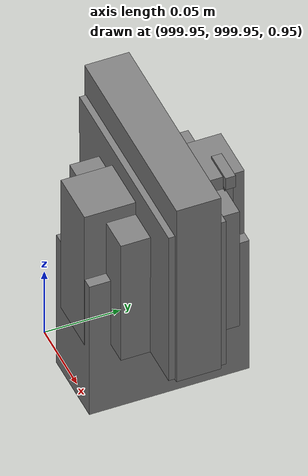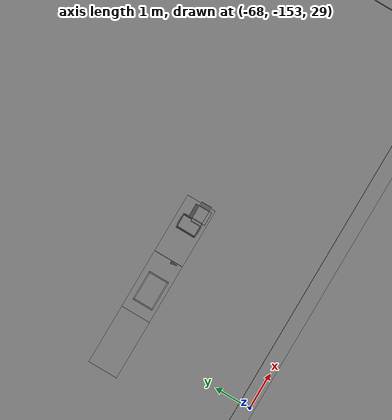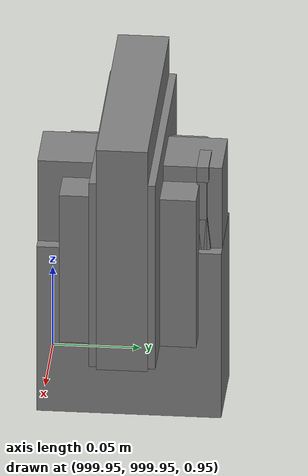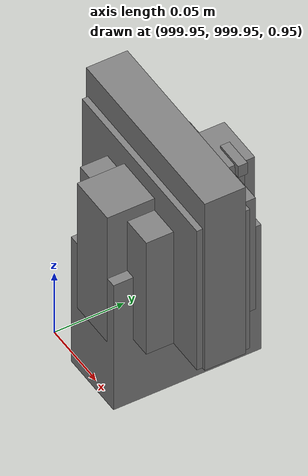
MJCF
<mujoco>
    <option gravity="0.000000000 0.000000000 -9.810000420" timestep="0.0049999999" integrator="implicitfast" density="1.225" viscosity="1.8000001e-05" noslip_iterations="10" iterations="100" sdf_iterations="50">
        <flag multiccd="disable"/>
    </option>
    <size memory="1000M"/>
    <compiler coordinate="local"/>
    <worldbody>
        <light cutoff="30" pos="0 1 1" dir="0 -1 -2"/>
        <light cutoff="30" pos="0 -1 1" dir="0 1 -2"/>
        <body pos="-64.866622925 -149.383972168 30.183746338" euler="89.999984741 89.999946594 0.000000000" name="openloong_gripper_2f85_fix_base_usda_bluebox_01">
            <geom contype="1" conaffinity="1" density="1000" type="box" material="" rgba="0.500000000 0.500000000 0.500000000 1.000000000" solimp="0.899999976 0.949999988 0.001000000" friction="1.000000000 0.005000000 0.000100000" solref="0.020000000 1.000000000" margin="0" condim="3" group="0" pos="0.276580811 0.187225342 0.000068665" quat="0.707106948 0.000077471 0.707106352 0.000077486" size="0.100000001 0.057999998 0.010000000" name="openloong_gripper_2f85_fix_base_usda_geom_A8DD4815_E384_4019_AAE8_7DB583D902C9"/>
            <geom contype="1" conaffinity="1" density="1000" type="box" material="" rgba="0.500000000 0.500000000 0.500000000 1.000000000" solimp="0.899999976 0.949999988 0.001000000" friction="1.000000000 0.005000000 0.000100000" solref="0.020000000 1.000000000" margin="0" condim="3" group="0" pos="0.000000000 0.002883911 0.000000000" quat="0.999999881 0.000000000 0.000000000 0.000000000" size="0.254000008 0.003000000 0.172000006" name="openloong_gripper_2f85_fix_base_usda_geom_AE40DE2F_DF88_46BF_B69C_11F60C1D2D52"/>
            <geom contype="1" conaffinity="1" density="1000" type="box" material="" rgba="0.500000000 0.500000000 0.500000000 1.000000000" solimp="0.899999976 0.949999988 0.001000000" friction="1.000000000 0.005000000 0.000100000" solref="0.020000000 1.000000000" margin="0" condim="3" group="0" pos="0.000000000 0.124874115 0.173484802" quat="0.999796331 0.020176515 -0.000000015 0.000000030" size="0.259999990 0.119999997 0.007000000" name="openloong_gripper_2f85_fix_base_usda_geom_1C64CC6A_CB91_46BB_8039_A65974207F7C"/>
            <geom contype="1" conaffinity="1" density="1000" type="box" material="" rgba="0.500000000 0.500000000 0.500000000 1.000000000" solimp="0.899999976 0.949999988 0.001000000" friction="1.000000000 0.005000000 0.000100000" solref="0.020000000 1.000000000" margin="0" condim="3" group="0" pos="0.000000000 0.124874115 -0.173469543" quat="0.999796331 -0.020176545 -0.000000015 0.000000000" size="0.259999990 0.119999997 0.007000000" name="openloong_gripper_2f85_fix_base_usda_geom_0959276A_8F39_4950_A15C_E75527E60DEF"/>
            <geom contype="1" conaffinity="1" density="1000" type="box" material="" rgba="0.500000000 0.500000000 0.500000000 1.000000000" solimp="0.899999976 0.949999988 0.001000000" friction="1.000000000 0.005000000 0.000100000" solref="0.020000000 1.000000000" margin="0" condim="3" group="0" pos="0.000000000 0.214008331 0.188980103" quat="0.999912977 0.013176724 0.000000015 0.000000000" size="0.259999990 0.029999999 0.012500000" name="openloong_gripper_2f85_fix_base_usda_geom_435172B2_82BF_4A2C_AC2A_F2EC187824C4"/>
            <geom contype="1" conaffinity="1" density="1000" type="box" material="" rgba="0.500000000 0.500000000 0.500000000 1.000000000" solimp="0.899999976 0.949999988 0.001000000" friction="1.000000000 0.005000000 0.000100000" solref="0.020000000 1.000000000" margin="0" condim="3" group="0" pos="-0.258361816 0.125289917 0.001876831" quat="0.702796936 -0.020792112 0.710783124 0.020769298" size="0.189999998 0.119999997 0.009000000" name="openloong_gripper_2f85_fix_base_usda_geom_0CF29A28_DD34_4E6A_82E9_1BFE909AEB5D"/>
            <geom contype="1" conaffinity="1" density="1000" type="box" material="" rgba="0.500000000 0.500000000 0.500000000 1.000000000" solimp="0.899999976 0.949999988 0.001000000" friction="1.000000000 0.005000000 0.000100000" solref="0.020000000 1.000000000" margin="0" condim="3" group="0" pos="0.000000000 0.214008331 -0.188980103" quat="0.999912977 -0.013176769 0.000000030 0.000000015" size="0.259999990 0.029999999 0.012500000" name="openloong_gripper_2f85_fix_base_usda_geom_3A2443ED_05F7_424A_85D0_4B9611E4D8BD"/>
            <geom contype="1" conaffinity="1" density="1000" type="box" material="" rgba="0.500000000 0.500000000 0.500000000 1.000000000" solimp="0.899999976 0.949999988 0.001000000" friction="1.000000000 0.005000000 0.000100000" solref="0.020000000 1.000000000" margin="0" condim="3" group="0" pos="-0.276611328 0.187225342 0.000068665" quat="0.707106650 0.000077441 0.707106709 0.000077456" size="0.100000001 0.057999998 0.010000000" name="openloong_gripper_2f85_fix_base_usda_geom_3643BCC4_7199_4E57_B4A8_A055F8611413"/>
            <geom contype="1" conaffinity="1" density="1000" type="box" material="" rgba="0.500000000 0.500000000 0.500000000 1.000000000" solimp="0.899999976 0.949999988 0.001000000" friction="1.000000000 0.005000000 0.000100000" solref="0.020000000 1.000000000" margin="0" condim="3" group="0" pos="0.258331299 0.125289917 0.001876831" quat="0.702851415 0.018856421 0.710823774 -0.019329369" size="0.189999998 0.119999997 0.009000000" name="openloong_gripper_2f85_fix_base_usda_geom_C3160A33_5FEF_438E_A78C_A846D2D93172"/>
            <freejoint name="openloong_gripper_2f85_fix_base_usda_bluebox_01_joint"/>
            <site size="0.005000000 0.005000000 0.005000000" rgba="0.500000000 0.500000000 0.500000000 1.000000000" pos="0.000000000 0.000000000 0.000000000" quat="0.999961913 0.008726534 0.000000000 0.000000000" group="0" type="sphere" name="openloong_gripper_2f85_fix_base_usda_bluebox_01site"/>
        </body>
        <body pos="-64.496299744 -149.491867065 30.235729218" euler="0.000000000 0.000000000 89.999946594" name="openloong_gripper_2f85_fix_base_usda_cardboardbox_01">
            <geom contype="1" conaffinity="1" density="1000" type="box" material="" rgba="0.500000000 0.500000000 0.500000000 1.000000000" solimp="0.899999976 0.949999988 0.001000000" friction="1.000000000 0.005000000 0.000100000" solref="0.020000000 1.000000000" margin="0" condim="3" group="0" pos="-0.003166199 -0.004086494 0.005052090" quat="1.000000000 0.000000000 0.000000000 0.000000000" size="0.142499998 0.177500010 0.005000000" name="openloong_gripper_2f85_fix_base_usda_geom_C7C5F1F2_522B_43AA_B0FB_7EDB75F356C1"/>
            <geom contype="1" conaffinity="1" density="1000" type="box" material="" rgba="0.500000000 0.500000000 0.500000000 1.000000000" solimp="0.899999976 0.949999988 0.001000000" friction="1.000000000 0.005000000 0.000100000" solref="0.020000000 1.000000000" margin="0" condim="3" group="0" pos="-0.003166199 0.170316696 0.150570869" quat="1.000000000 0.000000000 0.000000000 0.000000000" size="0.142499998 0.005000000 0.149999991" name="openloong_gripper_2f85_fix_base_usda_geom_EE2A9D3A_53EC_4D57_9071_2C253275471A"/>
            <geom contype="1" conaffinity="1" density="1000" type="box" material="" rgba="0.500000000 0.500000000 0.500000000 1.000000000" solimp="0.899999976 0.949999988 0.001000000" friction="1.000000000 0.005000000 0.000100000" solref="0.020000000 1.000000000" margin="0" condim="3" group="0" pos="-0.147399902 -0.005307198 0.150570869" quat="1.000000000 0.000000000 0.000000000 0.000000000" size="0.005000000 0.177500010 0.149999991" name="openloong_gripper_2f85_fix_base_usda_geom_C06E65CA_59AD_4B7C_8E59_372080D1C491"/>
            <geom contype="1" conaffinity="1" density="1000" type="box" material="" rgba="0.500000000 0.500000000 0.500000000 1.000000000" solimp="0.899999976 0.949999988 0.001000000" friction="1.000000000 0.005000000 0.000100000" solref="0.020000000 1.000000000" margin="0" condim="3" group="0" pos="0.140275955 -0.005307198 0.150570869" quat="1.000000000 0.000000000 0.000000000 0.000000000" size="0.005000000 0.177500010 0.149999991" name="openloong_gripper_2f85_fix_base_usda_geom_037B8A9C_5629_42A4_A79F_D225C334A6A4"/>
            <geom contype="1" conaffinity="1" density="1000" type="box" material="" rgba="0.500000000 0.500000000 0.500000000 1.000000000" solimp="0.899999976 0.949999988 0.001000000" friction="1.000000000 0.005000000 0.000100000" solref="0.020000000 1.000000000" margin="0" condim="3" group="0" pos="-0.003166199 -0.181550980 0.150570869" quat="1.000000000 0.000000000 0.000000000 0.000000000" size="0.142499998 0.005000000 0.149999991" name="openloong_gripper_2f85_fix_base_usda_geom_2442E20F_B856_45C2_969F_B2A1CD3CB088"/>
            <freejoint name="openloong_gripper_2f85_fix_base_usda_cardboardbox_01_joint"/>
            <site size="0.005000000 0.005000000 0.005000000" rgba="0.500000000 0.500000000 0.500000000 1.000000000" pos="0.000000000 0.000000000 0.000000000" quat="0.999961913 0.008726535 0.000000000 0.000000000" group="0" type="sphere" name="openloong_gripper_2f85_fix_base_usda_site_3DD4BC35_4B06_41A7_91B3_EEFAB044EC22"/>
            <body pos="0.139160156 -0.004048347 0.301930904" euler="-179.999954224 49.383502960 179.999954224" name="openloong_gripper_2f85_fix_base_usda_A1_006">
                <geom contype="1" conaffinity="1" density="1000" type="box" material="" rgba="0.500000000 0.500000000 0.500000000 1.000000000" solimp="0.899999976 0.949999988 0.001000000" friction="1.000000000 0.005000000 0.000100000" solref="0.020000000 1.000000000" margin="0" condim="3" group="0" pos="-0.071587563 0.000009537 0.001745224" quat="0.999999881 0.000000000 0.000000000 0.000000000" size="0.071249999 0.179999992 0.002500000" name="openloong_gripper_2f85_fix_base_usda_geom_A79A9162_B28C_44EA_866B_7BD9C9B3612A"/>
                <joint armature="0" stiffness="0.07" damping="0.0099999998" axis="0.000000 1.000000 0.000000" type="hinge" name="openloong_gripper_2f85_fix_base_usda_A1_006"/>
            </body>
            <body pos="-0.145902634 -0.004086494 0.301938057" euler="-180.000000000 -60.000011444 -180.000000000" name="openloong_gripper_2f85_fix_base_usda_A2_006">
                <geom contype="1" conaffinity="1" density="1000" type="box" material="" rgba="0.500000000 0.500000000 0.500000000 1.000000000" solimp="0.899999976 0.949999988 0.001000000" friction="1.000000000 0.005000000 0.000100000" solref="0.020000000 1.000000000" margin="0" condim="3" group="0" pos="0.071268082 0.000009537 0.002717972" quat="0.000002921 0.000000000 -0.000000030 0.999999881" size="0.071249999 0.179999992 0.002500000" name="openloong_gripper_2f85_fix_base_usda_geom_C9AA8896_F5EF_4ECC_BE2F_E78312D3AF38"/>
                <joint armature="0" stiffness="0.07" damping="0.0099999998" axis="0.000000 1.000000 0.000000" type="hinge" name="openloong_gripper_2f85_fix_base_usda_A2_006"/>
            </body>
            <body pos="-0.003385544 0.175991058 0.301930904" euler="-125.858116150 -0.000004561 0.000002331" name="openloong_gripper_2f85_fix_base_usda_B2_006">
                <geom contype="1" conaffinity="1" density="1000" type="box" material="" rgba="0.500000000 0.500000000 0.500000000 1.000000000" solimp="0.899999976 0.949999988 0.001000000" friction="1.000000000 0.005000000 0.000100000" solref="0.020000000 1.000000000" margin="0" condim="3" group="0" pos="0.000009537 -0.070939064 -0.002470016" quat="0.999614120 0.027776197 -0.000000015 0.000000030" size="0.137500003 0.064999998 0.005000000" name="openloong_gripper_2f85_fix_base_usda_geom_F766AFCC_DED8_46FF_AC24_27CB05C8326C"/>
                <joint armature="0" stiffness="0.07" damping="0.0099999998" axis="1.000000 0.000000 0.000000" type="hinge" name="openloong_gripper_2f85_fix_base_usda_B2_006"/>
            </body>
            <body pos="-0.003385544 -0.184140205 0.301938057" euler="147.805557251 0.000000000 0.000000000" name="openloong_gripper_2f85_fix_base_usda_B1_006">
                <geom contype="1" conaffinity="1" density="1000" type="box" material="" rgba="0.500000000 0.500000000 0.500000000 1.000000000" solimp="0.899999976 0.949999988 0.001000000" friction="1.000000000 0.005000000 0.000100000" solref="0.020000000 1.000000000" margin="0" condim="3" group="0" pos="-0.000028610 0.070202351 -0.002703667" quat="0.999614179 -0.027776167 0.000000000 0.000000000" size="0.137500003 0.064999998 0.005000000" name="openloong_gripper_2f85_fix_base_usda_geom_E2D06CF1_AF5E_4F26_80DD_E083E9CA5E4E"/>
                <joint armature="0" stiffness="0.07" damping="0.0099999998" axis="1.000000 0.000000 0.000000" type="hinge" name="openloong_gripper_2f85_fix_base_usda_B1_006"/>
            </body>
        </body>
        <body pos="-65.882858276 -149.481979370 30.229999542" euler="-64.487716675 0.000000000 0.000000000" name="openloong_gripper_2f85_fix_base_usda_Barcode">
            <geom contype="1" conaffinity="1" density="1000" type="box" material="" rgba="0.500000000 0.500000000 0.500000000 1.000000000" solimp="0.899999976 0.949999988 0.001000000" friction="1.000000000 0.005000000 0.000100000" solref="0.020000000 1.000000000" margin="0" condim="3" group="0" pos="0.000000000 0.013038635 0.001419067" quat="0.000000000 0.000000000 0.000000000 1.000000119" size="0.034000002 0.010000000 0.017999999" name="openloong_gripper_2f85_fix_base_usda_geom_A0843FCC_B178_458E_8B1B_B9035C192DC7"/>
            <geom contype="1" conaffinity="1" density="1000" type="box" material="" rgba="0.500000000 0.500000000 0.500000000 1.000000000" solimp="0.899999976 0.949999988 0.001000000" friction="1.000000000 0.005000000 0.000100000" solref="0.020000000 1.000000000" margin="0" condim="3" group="0" pos="0.000000000 -0.035301208 -0.007095337" quat="0.000000000 0.000000000 -0.043619365 0.999048233" size="0.028999999 0.010000000 0.020000000" name="openloong_gripper_2f85_fix_base_usda_geom_30B349A0_AA24_485B_865C_FACDBF63E1CA"/>
            <geom contype="1" conaffinity="1" density="1000" type="box" material="" rgba="0.500000000 0.500000000 0.500000000 1.000000000" solimp="0.899999976 0.949999988 0.001000000" friction="1.000000000 0.005000000 0.000100000" solref="0.020000000 1.000000000" margin="0" condim="3" group="0" pos="0.000000000 -0.043411255 -0.011749268" quat="0.922262907 0.386563420 0.000000000 0.000000000" size="0.026000001 0.010000000 0.020000000" name="openloong_gripper_2f85_fix_base_usda_geom_EE5FB814_35F4_4B06_9A33_FC3F70CCCFEB"/>
            <geom contype="1" conaffinity="1" density="1000" type="box" material="" rgba="0.500000000 0.500000000 0.500000000 1.000000000" solimp="0.899999976 0.949999988 0.001000000" friction="1.000000000 0.005000000 0.000100000" solref="0.020000000 1.000000000" margin="0" condim="3" group="0" pos="0.000000000 -0.016967773 -0.031860352" quat="0.000000000 0.000000000 0.000000000 1.000000119" size="0.008000000 0.010000000 0.013000000" name="openloong_gripper_2f85_fix_base_usda_geom_29F40C53_F8F4_438D_9988_4F0D122582A5"/>
            <geom contype="1" conaffinity="1" density="1000" type="box" material="" rgba="0.500000000 0.500000000 0.500000000 1.000000000" solimp="0.899999976 0.949999988 0.001000000" friction="1.000000000 0.005000000 0.000100000" solref="0.020000000 1.000000000" margin="0" condim="3" group="0" pos="0.000000000 -0.001869202 0.000312805" quat="0.953716993 0.300705761 0.000000000 0.000000000" size="0.032000002 0.010000000 0.018999999" name="openloong_gripper_2f85_fix_base_usda_geom_2C6B32B5_4A0A_4177_9E55_4229ED91190F"/>
            <geom contype="1" conaffinity="1" density="1000" type="box" material="" rgba="0.500000000 0.500000000 0.500000000 1.000000000" solimp="0.899999976 0.949999988 0.001000000" friction="1.000000000 0.005000000 0.000100000" solref="0.020000000 1.000000000" margin="0" condim="3" group="0" pos="0.000000000 -0.019531250 -0.003173828" quat="0.953716993 0.300705761 0.000000000 0.000000000" size="0.030999999 0.010000000 0.020000000" name="openloong_gripper_2f85_fix_base_usda_geom_84B85BD7_9EC5_4712_AFE1_54BCEDB16B2E"/>
            <geom contype="1" conaffinity="1" density="1000" type="box" material="" rgba="0.500000000 0.500000000 0.500000000 1.000000000" solimp="0.899999976 0.949999988 0.001000000" friction="1.000000000 0.005000000 0.000100000" solref="0.020000000 1.000000000" margin="0" condim="3" group="0" pos="0.000000000 -0.035301208 -0.007095337" quat="0.953716993 0.300705761 0.000000000 0.000000000" size="0.028999999 0.010000000 0.020000000" name="openloong_gripper_2f85_fix_base_usda_geom_CDB5BE67_197D_4F09_8BE0_350AC425A7DA"/>
            <geom contype="1" conaffinity="1" density="1000" type="box" material="" rgba="0.500000000 0.500000000 0.500000000 1.000000000" solimp="0.899999976 0.949999988 0.001000000" friction="1.000000000 0.005000000 0.000100000" solref="0.020000000 1.000000000" margin="0" condim="3" group="0" pos="0.000000000 -0.042617798 -0.071121216" quat="0.000000000 0.000000000 0.000000000 1.000000119" size="0.013000000 0.021000000 0.059999999" name="openloong_gripper_2f85_fix_base_usda_geom_13BB3165_88CE_4F3A_86CB_69A4FCA5CB08"/>
            <freejoint name="openloong_gripper_2f85_fix_base_usda_Barcode_joint"/>
            <site size="0.005000000 0.005000000 0.005000000" rgba="0.500000000 0.500000000 0.500000000 1.000000000" pos="0.000000000 0.000000000 0.000000000" quat="1.000000000 0.000000000 0.000000000 0.000000000" group="0" type="sphere" name="openloong_gripper_2f85_fix_base_usda_Barcode_site"/>
        </body>
        <body pos="-66.745018005 -149.392349243 30.184000015" euler="0.000000000 0.000000000 89.999946594" name="[22329808769305]_Basket_01">
            <geom contype="1" conaffinity="1" density="1000" type="box" material="" rgba="0.500000000 0.500000000 0.500000000 1.000000000" solimp="0.899999976 0.949999988 0.001000000" friction="1.000000000 0.005000000 0.000100000" solref="0.020000000 1.000000000" margin="0" condim="3" group="0" pos="-0.052425385 0.389207840 0.089787483" quat="0.707107008 0.000000000 0.000000000 0.707106411" size="0.014249999 0.014249999 0.059999999" name="[22329808769305]_geom_E7AEC970_1E9D_4057_97D1_1643B80B3C03"/>
            <geom contype="1" conaffinity="1" density="1000" type="box" material="" rgba="0.500000000 0.500000000 0.500000000 1.000000000" solimp="0.899999976 0.949999988 0.001000000" friction="1.000000000 0.005000000 0.000100000" solref="0.020000000 1.000000000" margin="0" condim="3" group="0" pos="0.264015198 -0.133043289 0.089787483" quat="0.707107008 0.000000000 0.000000000 0.707106411" size="0.014249999 0.014249999 0.059999999" name="[22329808769305]_geom_41694297_5A04_4871_89C7_7876CCF4D839"/>
            <geom contype="1" conaffinity="1" density="1000" type="box" material="" rgba="0.500000000 0.500000000 0.500000000 1.000000000" solimp="0.899999976 0.949999988 0.001000000" friction="1.000000000 0.005000000 0.000100000" solref="0.020000000 1.000000000" margin="0" condim="3" group="0" pos="-0.264015198 -0.265548706 0.089793205" quat="0.707107008 0.000000000 0.000000000 0.707106411" size="0.014249999 0.014249999 0.059999999" name="[22329808769305]_geom_8E566D80_0595_46CE_B749_ADCE83463C44"/>
            <geom contype="1" conaffinity="1" density="1000" type="box" material="" rgba="0.500000000 0.500000000 0.500000000 1.000000000" solimp="0.899999976 0.949999988 0.001000000" friction="1.000000000 0.005000000 0.000100000" solref="0.020000000 1.000000000" margin="0" condim="3" group="0" pos="-0.160263062 -0.389322281 0.089793205" quat="0.707107008 0.000000000 0.000000000 0.707106411" size="0.014249999 0.014249999 0.059999999" name="[22329808769305]_geom_AF575DDA_DAB4_4E86_9195_6C5719948A84"/>
            <geom contype="1" conaffinity="1" density="1000" type="box" material="" rgba="0.500000000 0.500000000 0.500000000 1.000000000" solimp="0.899999976 0.949999988 0.001000000" friction="1.000000000 0.005000000 0.000100000" solref="0.020000000 1.000000000" margin="0" condim="3" group="0" pos="0.162265778 -0.389322281 0.089787483" quat="0.707107008 0.000000000 0.000000000 0.707106411" size="0.014249999 0.014249999 0.059999999" name="[22329808769305]_geom_9B0A38D4_4629_47AC_9E26_4BCB8202D214"/>
            <geom contype="1" conaffinity="1" density="1000" type="box" material="" rgba="0.500000000 0.500000000 0.500000000 1.000000000" solimp="0.899999976 0.949999988 0.001000000" friction="1.000000000 0.005000000 0.000100000" solref="0.020000000 1.000000000" margin="0" condim="3" group="0" pos="0.264015198 0.389207840 0.089787483" quat="0.707107008 0.000000000 0.000000000 0.707106411" size="0.014249999 0.014249999 0.059999999" name="[22329808769305]_geom_FC1D1577_85D0_4039_8BE3_AD586C95C0E2"/>
            <geom contype="1" conaffinity="1" density="1000" type="box" material="" rgba="0.500000000 0.500000000 0.500000000 1.000000000" solimp="0.899999976 0.949999988 0.001000000" friction="1.000000000 0.005000000 0.000100000" solref="0.020000000 1.000000000" margin="0" condim="3" group="0" pos="-0.264015198 -0.133043289 0.089793205" quat="0.707107008 0.000000000 0.000000000 0.707106411" size="0.014249999 0.014249999 0.059999999" name="[22329808769305]_geom_A3B75D45_33FC_4DFA_B4C8_06CF7B4FC1DE"/>
            <geom contype="1" conaffinity="1" density="1000" type="box" material="" rgba="0.500000000 0.500000000 0.500000000 1.000000000" solimp="0.899999976 0.949999988 0.001000000" friction="1.000000000 0.005000000 0.000100000" solref="0.020000000 1.000000000" margin="0" condim="3" group="0" pos="-0.264026642 0.269256592 0.089793205" quat="0.707107008 0.000000000 0.000000000 0.707106411" size="0.014249999 0.014249999 0.059999999" name="[22329808769305]_geom_6D8E8EA5_31F5_495C_A9D8_7A485C604E30"/>
            <geom contype="1" conaffinity="1" density="1000" type="box" material="" rgba="0.500000000 0.500000000 0.500000000 1.000000000" solimp="0.899999976 0.949999988 0.001000000" friction="1.000000000 0.005000000 0.000100000" solref="0.020000000 1.000000000" margin="0" condim="3" group="0" pos="0.054462433 0.389207840 0.089787483" quat="0.707107008 0.000000000 0.000000000 0.707106411" size="0.014249999 0.014249999 0.059999999" name="[22329808769305]_geom_93E9F413_BEBA_458A_9925_60298737365E"/>
            <geom contype="1" conaffinity="1" density="1000" type="box" material="" rgba="0.500000000 0.500000000 0.500000000 1.000000000" solimp="0.899999976 0.949999988 0.001000000" friction="1.000000000 0.005000000 0.000100000" solref="0.020000000 1.000000000" margin="0" condim="3" group="0" pos="0.054462433 -0.389322281 0.089787483" quat="0.707107008 0.000000000 0.000000000 0.707106411" size="0.014249999 0.014249999 0.059999999" name="[22329808769305]_geom_2BF68C13_10C5_4F78_A0F2_358BAE545457"/>
            <geom contype="1" conaffinity="1" density="1000" type="box" material="" rgba="0.500000000 0.500000000 0.500000000 1.000000000" solimp="0.899999976 0.949999988 0.001000000" friction="1.000000000 0.005000000 0.000100000" solref="0.020000000 1.000000000" margin="0" condim="3" group="0" pos="0.264015198 0.269256592 0.089793205" quat="0.707107008 0.000000000 0.000000000 0.707106411" size="0.014249999 0.014249999 0.059999999" name="[22329808769305]_geom_F7C2A1E5_9CA1_4A0D_8F80_60121CF373A2"/>
            <geom contype="1" conaffinity="1" density="1000" type="box" material="" rgba="0.500000000 0.500000000 0.500000000 1.000000000" solimp="0.899999976 0.949999988 0.001000000" friction="1.000000000 0.005000000 0.000100000" solref="0.020000000 1.000000000" margin="0" condim="3" group="0" pos="0.264015198 -0.389322281 0.089787483" quat="0.707107008 0.000000000 0.000000000 0.707106411" size="0.014249999 0.014249999 0.059999999" name="[22329808769305]_geom_435E8B8A_0D79_40DD_94AA_B9D2C110076F"/>
            <geom contype="1" conaffinity="1" density="1000" type="box" material="" rgba="0.500000000 0.500000000 0.500000000 1.000000000" solimp="0.899999976 0.949999988 0.001000000" friction="1.000000000 0.005000000 0.000100000" solref="0.020000000 1.000000000" margin="0" condim="3" group="0" pos="0.000000000 0.000000000 0.015998840" quat="0.707107008 0.000000000 0.000000000 0.707106411" size="0.403499991 0.279000014 0.015750000" name="[22329808769305]_geom_3F89122D_E461_495D_84C5_32658938D019"/>
            <geom contype="1" conaffinity="1" density="1000" type="box" material="" rgba="0.500000000 0.500000000 0.500000000 1.000000000" solimp="0.899999976 0.949999988 0.001000000" friction="1.000000000 0.005000000 0.000100000" solref="0.020000000 1.000000000" margin="0" condim="3" group="0" pos="0.000000000 -0.389476776 0.163619041" quat="0.707107008 0.000000000 0.000000000 0.707106411" size="0.015000000 0.277500004 0.015750000" name="[22329808769305]_geom_D08794BC_105E_4E9D_8905_EDA7FA0EDC23"/>
            <geom contype="1" conaffinity="1" density="1000" type="box" material="" rgba="0.500000000 0.500000000 0.500000000 1.000000000" solimp="0.899999976 0.949999988 0.001000000" friction="1.000000000 0.005000000 0.000100000" solref="0.020000000 1.000000000" margin="0" condim="3" group="0" pos="0.162265778 0.389207840 0.089787483" quat="0.707107008 0.000000000 0.000000000 0.707106411" size="0.014249999 0.014249999 0.059999999" name="[22329808769305]_geom_97A79509_2893_463A_9892_84510EF626BB"/>
            <geom contype="1" conaffinity="1" density="1000" type="box" material="" rgba="0.500000000 0.500000000 0.500000000 1.000000000" solimp="0.899999976 0.949999988 0.001000000" friction="1.000000000 0.005000000 0.000100000" solref="0.020000000 1.000000000" margin="0" condim="3" group="0" pos="0.000000000 0.389471054 0.163619041" quat="0.707107008 0.000000000 0.000000000 0.707106411" size="0.015000000 0.277500004 0.015750000" name="[22329808769305]_geom_1D2EF3AD_F5AD_46E0_BF4E_5F4CEBE4107B"/>
            <geom contype="1" conaffinity="1" density="1000" type="box" material="" rgba="0.500000000 0.500000000 0.500000000 1.000000000" solimp="0.899999976 0.949999988 0.001000000" friction="1.000000000 0.005000000 0.000100000" solref="0.020000000 1.000000000" margin="0" condim="3" group="0" pos="-0.263511658 0.000000000 0.163619041" quat="0.707107008 0.000000000 0.000000000 0.707106411" size="0.403499991 0.015000000 0.015750000" name="[22329808769305]_geom_EC86DBC8_A34A_46B1_B0C6_8766A8330618"/>
            <geom contype="1" conaffinity="1" density="1000" type="box" material="" rgba="0.500000000 0.500000000 0.500000000 1.000000000" solimp="0.899999976 0.949999988 0.001000000" friction="1.000000000 0.005000000 0.000100000" solref="0.020000000 1.000000000" margin="0" condim="3" group="0" pos="-0.264015198 0.141334534 0.089793205" quat="0.707107008 0.000000000 0.000000000 0.707106411" size="0.014249999 0.014249999 0.059999999" name="[22329808769305]_geom_15F53288_79DC_40C4_B876_6923FE1E0400"/>
            <geom contype="1" conaffinity="1" density="1000" type="box" material="" rgba="0.500000000 0.500000000 0.500000000 1.000000000" solimp="0.899999976 0.949999988 0.001000000" friction="1.000000000 0.005000000 0.000100000" solref="0.020000000 1.000000000" margin="0" condim="3" group="0" pos="0.264015198 -0.265548706 0.089787483" quat="0.707107008 0.000000000 0.000000000 0.707106411" size="0.014249999 0.014249999 0.059999999" name="[22329808769305]_geom_0802D75C_A572_4BC0_BB66_1A3EAE4E9563"/>
            <geom contype="1" conaffinity="1" density="1000" type="box" material="" rgba="0.500000000 0.500000000 0.500000000 1.000000000" solimp="0.899999976 0.949999988 0.001000000" friction="1.000000000 0.005000000 0.000100000" solref="0.020000000 1.000000000" margin="0" condim="3" group="0" pos="-0.160263062 0.389207840 0.089787483" quat="0.707107008 0.000000000 0.000000000 0.707106411" size="0.014249999 0.014249999 0.059999999" name="[22329808769305]_geom_4DEAC604_1D78_4CAF_94E8_C5D097E46334"/>
            <geom contype="1" conaffinity="1" density="1000" type="box" material="" rgba="0.500000000 0.500000000 0.500000000 1.000000000" solimp="0.899999976 0.949999988 0.001000000" friction="1.000000000 0.005000000 0.000100000" solref="0.020000000 1.000000000" margin="0" condim="3" group="0" pos="-0.052425385 -0.389322281 0.089787483" quat="0.707107008 0.000000000 0.000000000 0.707106411" size="0.014249999 0.014249999 0.059999999" name="[22329808769305]_geom_93AA866A_F8C2_4FF5_AA47_920009F1ECA7"/>
            <geom contype="1" conaffinity="1" density="1000" type="box" material="" rgba="0.500000000 0.500000000 0.500000000 1.000000000" solimp="0.899999976 0.949999988 0.001000000" friction="1.000000000 0.005000000 0.000100000" solref="0.020000000 1.000000000" margin="0" condim="3" group="0" pos="-0.264026642 -0.389322281 0.089793205" quat="0.707107008 0.000000000 0.000000000 0.707106411" size="0.014249999 0.014249999 0.059999999" name="[22329808769305]_geom_57A1ABC8_295C_4B62_B4FC_D6100C2BDF2B"/>
            <geom contype="1" conaffinity="1" density="1000" type="box" material="" rgba="0.500000000 0.500000000 0.500000000 1.000000000" solimp="0.899999976 0.949999988 0.001000000" friction="1.000000000 0.005000000 0.000100000" solref="0.020000000 1.000000000" margin="0" condim="3" group="0" pos="0.264015198 0.141334534 0.089787483" quat="0.707107008 0.000000000 0.000000000 0.707106411" size="0.014249999 0.014249999 0.059999999" name="[22329808769305]_geom_2F736552_F27A_48EE_B3CE_C139E015633F"/>
            <geom contype="1" conaffinity="1" density="1000" type="box" material="" rgba="0.500000000 0.500000000 0.500000000 1.000000000" solimp="0.899999976 0.949999988 0.001000000" friction="1.000000000 0.005000000 0.000100000" solref="0.020000000 1.000000000" margin="0" condim="3" group="0" pos="-0.264015198 0.389207840 0.089793205" quat="0.707107008 0.000000000 0.000000000 0.707106411" size="0.014249999 0.014249999 0.059999999" name="[22329808769305]_geom_6047734D_E5FF_475B_8C5D_480E1422BDF2"/>
            <geom contype="1" conaffinity="1" density="1000" type="box" material="" rgba="0.500000000 0.500000000 0.500000000 1.000000000" solimp="0.899999976 0.949999988 0.001000000" friction="1.000000000 0.005000000 0.000100000" solref="0.020000000 1.000000000" margin="0" condim="3" group="0" pos="0.264015198 0.004480362 0.089787483" quat="0.707107008 0.000000000 0.000000000 0.707106411" size="0.014249999 0.014249999 0.059999999" name="[22329808769305]_geom_515613D8_84BE_4090_9DC4_91A875362E96"/>
            <geom contype="1" conaffinity="1" density="1000" type="box" material="" rgba="0.500000000 0.500000000 0.500000000 1.000000000" solimp="0.899999976 0.949999988 0.001000000" friction="1.000000000 0.005000000 0.000100000" solref="0.020000000 1.000000000" margin="0" condim="3" group="0" pos="0.263694763 -0.000011444 0.163619041" quat="0.707107008 0.000000000 0.000000000 0.707106411" size="0.403499991 0.015000000 0.015750000" name="[22329808769305]_geom_FA493476_37B0_45B6_ACC8_E5DAF6B0119F"/>
            <geom contype="1" conaffinity="1" density="1000" type="box" material="" rgba="0.500000000 0.500000000 0.500000000 1.000000000" solimp="0.899999976 0.949999988 0.001000000" friction="1.000000000 0.005000000 0.000100000" solref="0.020000000 1.000000000" margin="0" condim="3" group="0" pos="-0.264015198 0.004480362 0.089793205" quat="0.707107008 0.000000000 0.000000000 0.707106411" size="0.014249999 0.014249999 0.059999999" name="[22329808769305]_geom_805087C8_740D_41D9_BE90_DD0885B57D62"/>
            <freejoint name="[22329808769305]_joint_67621B1D_7899_4115_9A98_61DE43AC1F55"/>
        </body>
        <body pos="0.000000000 0.000000000 0.000000000" euler="0.000000000 0.000000000 0.000000000" name="Static Objects_Static Objects">
            <geom contype="1" conaffinity="1" density="1000" type="box" material="" rgba="0.500000000 0.500000000 0.500000000 1.000000000" solimp="0.899999976 0.949999988 0.001000000" friction="1.000000000 0.005000000 0.000100000" solref="0.020000000 1.000000000" margin="0" condim="3" group="0" pos="-67.544113159 -149.365814209 29.727830887" quat="0.500000417 0.499999970 0.499999553 0.499999970" size="0.381000012 0.319999993 0.041000001" name="Static Objects_geom_6BFDF825_FD0B_449E_ACC2_6DBBC78532B0"/>
            <geom contype="1" conaffinity="1" density="1000" type="box" material="" rgba="0.500000000 0.500000000 0.500000000 1.000000000" solimp="0.899999976 0.949999988 0.001000000" friction="1.000000000 0.005000000 0.000100000" solref="0.020000000 1.000000000" margin="0" condim="3" group="0" pos="-68.239501953 -149.365814209 30.086868286" quat="0.500000417 0.499999970 0.499999553 0.499999970" size="0.370999992 0.039500002 0.745000005" name="Static Objects_geom_3480ED27_7E42_4CDC_8E68_5E90B9FC544D"/>
            <geom contype="1" conaffinity="1" density="1000" type="box" material="" rgba="0.500000000 0.500000000 0.500000000 1.000000000" solimp="0.899999976 0.949999988 0.001000000" friction="1.000000000 0.005000000 0.000100000" solref="0.020000000 1.000000000" margin="0" condim="3" group="0" pos="-68.239501953 -149.365814209 30.147235870" quat="0.500000417 0.499999970 0.499999553 0.499999970" size="0.400000006 0.022000000 0.800000012" name="Static Objects_geom_BB96871B_08AF_4F67_8214_E72B79883B42"/>
            <geom contype="1" conaffinity="1" density="1000" type="box" material="" rgba="0.500000000 0.500000000 0.500000000 1.000000000" solimp="0.899999976 0.949999988 0.001000000" friction="1.000000000 0.005000000 0.000100000" solref="0.020000000 1.000000000" margin="0" condim="3" group="0" pos="-68.934890747 -149.365814209 29.727830887" quat="0.500000417 0.499999970 0.499999553 0.499999970" size="0.381000012 0.319999993 0.041000001" name="Static Objects_geom_A67A5DB8_FF23_4207_8ADA_6AC9AB6CEAF2"/>
            <geom contype="1" conaffinity="1" density="1000" type="box" material="" rgba="0.500000000 0.500000000 0.500000000 1.000000000" solimp="0.899999976 0.949999988 0.001000000" friction="1.000000000 0.005000000 0.000100000" solref="0.020000000 1.000000000" margin="0" condim="3" group="0" pos="-68.239501953 -149.365814209 29.561563492" quat="0.500000417 0.499999970 0.499999553 0.499999970" size="0.020000000 0.022000000 0.660000026" name="Static Objects_geom_18BABA04_C48B_41DF_8041_8292F4F34B88"/>
            <geom contype="1" conaffinity="1" density="1000" type="box" material="" rgba="0.500000000 0.500000000 0.500000000 1.000000000" solimp="0.899999976 0.949999988 0.001000000" friction="1.000000000 0.005000000 0.000100000" solref="0.020000000 1.000000000" margin="0" condim="3" group="0" pos="-65.945671082 -149.365814209 29.727830887" quat="0.500000417 0.499999970 0.499999553 0.499999970" size="0.381000012 0.319999993 0.041000001" name="Static Objects_geom_DE4B53A2_630A_413B_8C78_8D0FFF0C7ABA"/>
            <geom contype="1" conaffinity="1" density="1000" type="box" material="" rgba="0.500000000 0.500000000 0.500000000 1.000000000" solimp="0.899999976 0.949999988 0.001000000" friction="1.000000000 0.005000000 0.000100000" solref="0.020000000 1.000000000" margin="0" condim="3" group="0" pos="-66.641059875 -149.365814209 30.086868286" quat="0.500000417 0.499999970 0.499999553 0.499999970" size="0.370999992 0.039500002 0.745000005" name="Static Objects_geom_DD31E776_19FB_4A93_9CBC_92FC126D3F34"/>
            <geom contype="1" conaffinity="1" density="1000" type="box" material="" rgba="0.500000000 0.500000000 0.500000000 1.000000000" solimp="0.899999976 0.949999988 0.001000000" friction="1.000000000 0.005000000 0.000100000" solref="0.020000000 1.000000000" margin="0" condim="3" group="0" pos="-66.641059875 -149.365814209 30.147235870" quat="0.500000417 0.499999970 0.499999553 0.499999970" size="0.400000006 0.022000000 0.800000012" name="Static Objects_geom_A267BF46_3693_441A_8FC9_80C321884711"/>
            <geom contype="1" conaffinity="1" density="1000" type="box" material="" rgba="0.500000000 0.500000000 0.500000000 1.000000000" solimp="0.899999976 0.949999988 0.001000000" friction="1.000000000 0.005000000 0.000100000" solref="0.020000000 1.000000000" margin="0" condim="3" group="0" pos="-67.336448669 -149.365814209 29.727830887" quat="0.500000417 0.499999970 0.499999553 0.499999970" size="0.381000012 0.319999993 0.041000001" name="Static Objects_geom_B21A66DE_E386_4AA9_BABF_B238B1C72EF9"/>
            <geom contype="1" conaffinity="1" density="1000" type="box" material="" rgba="0.500000000 0.500000000 0.500000000 1.000000000" solimp="0.899999976 0.949999988 0.001000000" friction="1.000000000 0.005000000 0.000100000" solref="0.020000000 1.000000000" margin="0" condim="3" group="0" pos="-66.641059875 -149.365814209 29.561563492" quat="0.500000417 0.499999970 0.499999553 0.499999970" size="0.020000000 0.022000000 0.660000026" name="Static Objects_geom_DADFFEA3_5CEB_4964_ACBC_2FBE44CAAC9E"/>
            <geom contype="1" conaffinity="1" density="1000" type="box" material="" rgba="0.500000000 0.500000000 0.500000000 1.000000000" solimp="0.899999976 0.949999988 0.001000000" friction="1.000000000 0.005000000 0.000100000" solref="0.020000000 1.000000000" margin="0" condim="3" group="0" pos="-64.338577271 -149.365814209 29.727830887" quat="0.500000417 0.499999970 0.499999553 0.499999970" size="0.381000012 0.319999993 0.041000001" name="Static Objects_geom_F8581C94_EBA3_451D_BF03_7A8B48A9B2BF"/>
            <geom contype="1" conaffinity="1" density="1000" type="box" material="" rgba="0.500000000 0.500000000 0.500000000 1.000000000" solimp="0.899999976 0.949999988 0.001000000" friction="1.000000000 0.005000000 0.000100000" solref="0.020000000 1.000000000" margin="0" condim="3" group="0" pos="-65.033966064 -149.365814209 30.086868286" quat="0.500000417 0.499999970 0.499999553 0.499999970" size="0.370999992 0.039500002 0.745000005" name="Static Objects_geom_ABD60984_D8C1_4F35_882F_0ED53FC39B0F"/>
            <geom contype="1" conaffinity="1" density="1000" type="box" material="" rgba="0.500000000 0.500000000 0.500000000 1.000000000" solimp="0.899999976 0.949999988 0.001000000" friction="1.000000000 0.005000000 0.000100000" solref="0.020000000 1.000000000" margin="0" condim="3" group="0" pos="-65.033966064 -149.365814209 30.147235870" quat="0.500000417 0.499999970 0.499999553 0.499999970" size="0.400000006 0.022000000 0.800000012" name="Static Objects_geom_3F47F223_3DE4_4C52_AF9E_FFDCD9D75920"/>
            <geom contype="1" conaffinity="1" density="1000" type="box" material="" rgba="0.500000000 0.500000000 0.500000000 1.000000000" solimp="0.899999976 0.949999988 0.001000000" friction="1.000000000 0.005000000 0.000100000" solref="0.020000000 1.000000000" margin="0" condim="3" group="0" pos="-65.729354858 -149.365814209 29.727830887" quat="0.500000417 0.499999970 0.499999553 0.499999970" size="0.381000012 0.319999993 0.041000001" name="Static Objects_geom_8036BC17_8991_4B49_A70C_591191D376A0"/>
            <geom contype="1" conaffinity="1" density="1000" type="box" material="" rgba="0.500000000 0.500000000 0.500000000 1.000000000" solimp="0.899999976 0.949999988 0.001000000" friction="1.000000000 0.005000000 0.000100000" solref="0.020000000 1.000000000" margin="0" condim="3" group="0" pos="-65.033966064 -149.365814209 29.561563492" quat="0.500000417 0.499999970 0.499999553 0.499999970" size="0.020000000 0.022000000 0.660000026" name="Static Objects_geom_AFC563AF_3F12_4154_AA0B_EEB0ED2899AE"/>
            <geom contype="1" conaffinity="1" density="1000" type="box" material="" rgba="0.500000000 0.500000000 0.500000000 1.000000000" solimp="0.899999976 0.949999988 0.001000000" friction="1.000000000 0.005000000 0.000100000" solref="0.020000000 1.000000000" margin="0" condim="3" group="0" pos="-61.754566193 -137.853729248 33.906845093" quat="0.707107067 0.000000000 0.000000000 0.707106471" size="0.759999990 0.759999990 4.500000000" name="Static Objects_geom_F91B2726_0714_44E4_8B84_706AF95B0398"/>
            <geom contype="1" conaffinity="1" density="1000" type="box" material="" rgba="0.500000000 0.500000000 0.500000000 1.000000000" solimp="0.899999976 0.949999988 0.001000000" friction="1.000000000 0.005000000 0.000100000" solref="0.020000000 1.000000000" margin="0" condim="3" group="0" pos="-57.511135101 -144.927108765 31.707921982" quat="1.000000000 0.000000000 0.000000000 0.000000000" size="0.200000003 8.000000000 2.299999952" name="Static Objects_geom_877FE565_AB54_4DBF_9D41_74F13DA20CE2"/>
            <geom contype="1" conaffinity="1" density="1000" type="box" material="" rgba="0.500000000 0.500000000 0.500000000 1.000000000" solimp="0.899999976 0.949999988 0.001000000" friction="1.000000000 0.005000000 0.000100000" solref="0.020000000 1.000000000" margin="0" condim="3" group="0" pos="-80.517646790 -157.574050903 31.688196182" quat="0.707107067 0.000000000 0.000000000 0.707106471" size="0.600000024 0.600000024 2.299999952" name="Static Objects_geom_61AFA9B5_EEEC_40E1_9E01_6F3352568F23"/>
            <geom contype="1" conaffinity="1" density="1000" type="box" material="" rgba="0.500000000 0.500000000 0.500000000 1.000000000" solimp="0.899999976 0.949999988 0.001000000" friction="1.000000000 0.005000000 0.000100000" solref="0.020000000 1.000000000" margin="0" condim="3" group="0" pos="-80.711044312 -147.414932251 31.666158676" quat="1.000000000 0.000000000 0.000000000 0.000000000" size="0.200000003 10.000000000 2.299999952" name="Static Objects_geom_CB22CA75_ED7F_4DCA_9A24_B5C72C3242D1"/>
            <geom contype="1" conaffinity="1" density="1000" type="box" material="" rgba="0.500000000 0.500000000 0.500000000 1.000000000" solimp="0.899999976 0.949999988 0.001000000" friction="1.000000000 0.005000000 0.000100000" solref="0.020000000 1.000000000" margin="0" condim="3" group="0" pos="-57.687217712 -137.434692383 31.688196182" quat="0.707107067 0.000000000 0.000000000 0.707106471" size="0.600000024 0.600000024 2.299999952" name="Static Objects_geom_CC4AE6B3_FA79_4C31_9968_EF2F09CC36F0"/>
            <geom contype="1" conaffinity="1" density="1000" type="box" material="" rgba="0.500000000 0.500000000 0.500000000 1.000000000" solimp="0.899999976 0.949999988 0.001000000" friction="1.000000000 0.005000000 0.000100000" solref="0.020000000 1.000000000" margin="0" condim="3" group="0" pos="-69.537033081 -140.263229370 31.714921951" quat="0.707107067 0.000000000 0.000000000 0.707106471" size="0.759999990 4.500000000 2.299999952" name="Static Objects_geom_19C7BB5A_A700_4252_AA85_4A45AFFE8C65"/>
            <geom contype="1" conaffinity="1" density="1000" type="box" material="" rgba="0.500000000 0.500000000 0.500000000 1.000000000" solimp="0.899999976 0.949999988 0.001000000" friction="1.000000000 0.005000000 0.000100000" solref="0.020000000 1.000000000" margin="0" condim="3" group="0" pos="-80.073638916 -137.853713989 33.906845093" quat="0.707107067 0.000000000 0.000000000 0.707106471" size="0.759999990 0.759999990 4.500000000" name="Static Objects_geom_EE8CCE25_0B41_4BF1_8CCC_A342CDD9B6F2"/>
            <geom contype="1" conaffinity="1" density="1000" type="box" material="" rgba="0.500000000 0.500000000 0.500000000 1.000000000" solimp="0.899999976 0.949999988 0.001000000" friction="1.000000000 0.005000000 0.000100000" solref="0.020000000 1.000000000" margin="0" condim="3" group="0" pos="-73.406707764 -155.734664917 31.707921982" quat="1.000000000 0.000000000 0.000000000 0.000000000" size="0.200000003 3.000000000 2.299999952" name="Static Objects_geom_D1D2253D_0EEF_4117_8035_0FB95E03266E"/>
            <geom contype="1" conaffinity="1" density="1000" type="box" material="" rgba="0.500000000 0.500000000 0.500000000 1.000000000" solimp="0.899999976 0.949999988 0.001000000" friction="1.000000000 0.005000000 0.000100000" solref="0.020000000 1.000000000" margin="0" condim="3" group="0" pos="-68.497543335 -137.448257446 31.707921982" quat="0.707107067 0.000000000 0.000000000 0.707106471" size="0.200000003 14.000000000 2.299999952" name="Static Objects_geom_033ED279_A251_452D_9178_F6CC8AB40944"/>
            <geom contype="1" conaffinity="1" density="1000" type="cylinder" material="" rgba="0.500000000 0.500000000 0.500000000 1.000000000" solimp="0.899999976 0.949999988 0.001000000" friction="1.000000000 0.005000000 0.000100000" solref="0.020000000 1.000000000" margin="0" condim="3" group="0" pos="-68.868522644 -142.134506226 31.711090088" quat="0.707107067 0.000000000 0.000000000 0.707106471" size="0.509999990 2.299999952 1.000000000" name="Static Objects_geom_2BFF12C2_E6E0_41C3_9B32_5DE4598C39A8"/>
            <geom contype="1" conaffinity="1" density="1000" type="plane" material="" rgba="0.500000000 0.500000000 0.500000000 1.000000000" solimp="0.899999976 0.949999988 0.001000000" friction="1.000000000 0.005000000 0.000100000" solref="0.020000000 1.000000000" margin="0" condim="3" group="0" pos="-72.873703003 -147.131927490 29.409669876" quat="1.000000000 0.000000000 0.000000000 0.000000000" size="18.000000000 14.000000000 1.000000000" name="Static Objects_geom_86A996BE_B85A_43DE_ADC7_D6CCD1CA398D"/>
            <geom contype="1" conaffinity="1" density="1000" type="box" material="" rgba="0.500000000 0.500000000 0.500000000 1.000000000" solimp="0.899999976 0.949999988 0.001000000" friction="1.000000000 0.005000000 0.000100000" solref="0.020000000 1.000000000" margin="0" condim="3" group="0" pos="-79.943580627 -157.782272339 31.707921982" quat="0.707107067 0.000000000 0.000000000 0.707106471" size="0.200000003 7.000000000 2.299999952" name="Static Objects_geom_C3307801_9271_4514_9812_D3FA81FE7B85"/>
            <geom contype="1" conaffinity="1" density="1000" type="box" material="" rgba="0.500000000 0.500000000 0.500000000 1.000000000" solimp="0.899999976 0.949999988 0.001000000" friction="1.000000000 0.005000000 0.000100000" solref="0.020000000 1.000000000" margin="0" condim="3" group="0" pos="-65.421028137 -152.903442383 31.707921982" quat="0.707107067 0.000000000 0.000000000 0.707106471" size="0.200000003 7.800000191 2.299999952" name="Static Objects_geom_370C854F_20F6_446D_B54D_F971EFC12FBE"/>
            <geom contype="1" conaffinity="1" density="1000" type="box" material="" rgba="0.500000000 0.500000000 0.500000000 1.000000000" solimp="0.899999976 0.949999988 0.001000000" friction="1.000000000 0.005000000 0.000100000" solref="0.020000000 1.000000000" margin="0" condim="3" group="0" pos="-74.776908875 -149.964416504 31.688196182" quat="1.000000000 0.000000000 0.000000000 0.000000000" size="0.600000024 0.409999996 2.299999952" name="Static Objects_geom_F03250A6_B35F_4599_92E2_4B84D22461C1"/>
            <geom contype="1" conaffinity="1" density="1000" type="cylinder" material="" rgba="0.500000000 0.500000000 0.500000000 1.000000000" solimp="0.899999976 0.949999988 0.001000000" friction="1.000000000 0.005000000 0.000100000" solref="0.020000000 1.000000000" margin="0" condim="3" group="0" pos="-60.161884308 -142.134506226 31.711090088" quat="0.707107067 0.000000000 0.000000000 0.707106471" size="0.509999990 2.299999952 1.000000000" name="Static Objects_geom_5D03B0F1_EF3C_4E82_A5CD_E5CD5A3C6E53"/>
            <geom contype="1" conaffinity="1" density="1000" type="cylinder" material="" rgba="0.500000000 0.500000000 0.500000000 1.000000000" solimp="0.899999976 0.949999988 0.001000000" friction="1.000000000 0.005000000 0.000100000" solref="0.020000000 1.000000000" margin="0" condim="3" group="0" pos="-75.382453918 -149.963455200 31.711090088" quat="0.707107067 0.000000000 0.000000000 0.707106471" size="0.409999996 2.299999952 1.000000000" name="Static Objects_geom_2F91EC84_4ABA_4EEF_BA77_DB5FD872AA9E"/>
            <geom contype="1" conaffinity="1" density="1000" type="cylinder" material="" rgba="0.500000000 0.500000000 0.500000000 1.000000000" solimp="0.899999976 0.949999988 0.001000000" friction="1.000000000 0.005000000 0.000100000" solref="0.020000000 1.000000000" margin="0" condim="3" group="0" pos="-74.154960632 -149.963455200 31.711090088" quat="0.707107067 0.000000000 0.000000000 0.707106471" size="0.409999996 2.299999952 1.000000000" name="Static Objects_geom_E67C7BB3_9393_42C0_82D0_726478B83B6B"/>
            <geom contype="1" conaffinity="1" density="1000" type="cylinder" material="" rgba="0.500000000 0.500000000 0.500000000 1.000000000" solimp="0.899999976 0.949999988 0.001000000" friction="1.000000000 0.005000000 0.000100000" solref="0.020000000 1.000000000" margin="0" condim="3" group="0" pos="-77.566612244 -142.134506226 31.711090088" quat="0.707107067 0.000000000 0.000000000 0.707106471" size="0.509999990 2.299999952 1.000000000" name="Static Objects_geom_44277871_1464_49D6_9A7E_577B659FC9D0"/>
        </body>
        <body pos="-66.279457092 -148.878204346 31.168344498" euler="-36.703247070 -51.233787537 57.864212036" mocap="true" name="spotlight1_SpotLight"/>
        <body pos="1000.000000000 1000.000000000 1.000000000" euler="0.000011953 0.000005123 -179.999984741" name="openloong_gripper_2f85_fix_base_usda_intel_box">
            <geom contype="1" conaffinity="1" density="1000" type="box" material="" rgba="0.500000000 0.500000000 0.500000000 1.000000000" solimp="0.899999976 0.949999988 0.001000000" friction="1.000000000 0.005000000 0.000100000" solref="0.020000000 1.000000000" margin="0" condim="3" group="0" pos="0.000000000 -0.000067139 0.000082284" quat="0.707106709 0.000000225 0.000000253 0.707106650" size="0.052800003 0.025300000 0.052800003" name="openloong_gripper_2f85_fix_base_usda_geom_DB699EF6_C96C_4CEC_B06F_266912110F2B"/>
            <freejoint name="openloong_gripper_2f85_fix_base_usda_intel_box_joint"/>
            <site size="0.005000000 0.005000000 0.005000000" rgba="0.500000000 0.500000000 0.500000000 1.000000000" pos="0.000000000 0.000000000 0.000000000" quat="0.999961913 0.008726500 0.000000000 0.000000000" group="0" type="sphere" name="openloong_gripper_2f85_fix_base_usda_intel_boxsite"/>
        </body>
        <body pos="1000.000000000 1000.000000000 1.000000000" euler="0.000000000 0.000000000 180.000000000" name="openloong_gripper_2f85_fix_base_usda_cpu_fan">
            <geom contype="1" conaffinity="1" density="1000" type="box" material="" rgba="0.500000000 0.500000000 0.500000000 1.000000000" solimp="0.899999976 0.949999988 0.001000000" friction="1.000000000 0.005000000 0.000100000" solref="0.020000000 1.000000000" margin="0" condim="3" group="0" pos="0.000000000 0.000000000 0.070034981" quat="0.000000000 0.000000000 0.000000000 1.000000000" size="0.070700005 0.014699999 0.070700005" name="openloong_gripper_2f85_fix_base_usda_geom_A05801E2_D3D2_4CE1_8522_EC61571EF9FF"/>
            <freejoint name="openloong_gripper_2f85_fix_base_usda_cpu_fan_joint"/>
            <site size="0.005000000 0.005000000 0.005000000" rgba="0.500000000 0.500000000 0.500000000 1.000000000" pos="0.000000000 0.000000000 0.000000000" quat="0.999961913 0.008726535 0.000000000 0.000000000" group="0" type="sphere" name="openloong_gripper_2f85_fix_base_usda_cpu_fancsite"/>
        </body>
        <body pos="1000.000000000 1000.000000000 1.000000000" euler="0.000000000 0.000000000 180.000000000" name="openloong_gripper_2f85_fix_base_usda_battery_01">
            <geom contype="1" conaffinity="1" density="1000" type="box" material="" rgba="0.500000000 0.500000000 0.500000000 1.000000000" solimp="0.899999976 0.949999988 0.001000000" friction="1.000000000 0.005000000 0.000100000" solref="0.020000000 1.000000000" margin="0" condim="3" group="0" pos="-0.011123657 -0.041940309 0.101691343" quat="1.000000000 0.000000000 0.000000000 0.000000000" size="0.010800000 0.003375000 0.004725000" name="openloong_gripper_2f85_fix_base_usda_geom_8CD38A83_0D54_4C2E_B1BC_8725B3E8B240"/>
            <geom contype="1" conaffinity="1" density="1000" type="box" material="" rgba="0.500000000 0.500000000 0.500000000 1.000000000" solimp="0.899999976 0.949999988 0.001000000" friction="1.000000000 0.005000000 0.000100000" solref="0.020000000 1.000000000" margin="0" condim="3" group="0" pos="-0.010876465 -0.044247437 0.047066893" quat="0.998702705 -0.050920475 0.000000000 0.000000000" size="0.009450001 0.002700000 0.024975000" name="openloong_gripper_2f85_fix_base_usda_geom_CDBAC0C7_8896_40B5_AFBD_8AC4F178E226"/>
            <geom contype="1" conaffinity="1" density="1000" type="box" material="" rgba="0.500000000 0.500000000 0.500000000 1.000000000" solimp="0.899999976 0.949999988 0.001000000" friction="1.000000000 0.005000000 0.000100000" solref="0.020000000 1.000000000" margin="0" condim="3" group="0" pos="-0.001235962 -0.000659180 0.047381196" quat="1.000000000 0.000000000 0.000000000 0.000000000" size="0.039420001 0.039150000 0.047250003" name="openloong_gripper_2f85_fix_base_usda_geom_E3D14E42_F0C8_4D96_B5AA_629BDA7973F8"/>
            <geom contype="1" conaffinity="1" density="1000" type="box" material="" rgba="0.500000000 0.500000000 0.500000000 1.000000000" solimp="0.899999976 0.949999988 0.001000000" friction="1.000000000 0.005000000 0.000100000" solref="0.020000000 1.000000000" margin="0" condim="3" group="0" pos="-0.010876465 -0.039138794 0.009851727" quat="1.000000000 0.000000000 0.000000000 0.000000000" size="0.009450001 0.010800000 0.013500000" name="openloong_gripper_2f85_fix_base_usda_geom_0FAD9DB2_7743_433B_8CA3_5191CB963610"/>
            <geom contype="1" conaffinity="1" density="1000" type="box" material="" rgba="0.500000000 0.500000000 0.500000000 1.000000000" solimp="0.899999976 0.949999988 0.001000000" friction="1.000000000 0.005000000 0.000100000" solref="0.020000000 1.000000000" margin="0" condim="3" group="0" pos="-0.010876465 -0.041528322 0.071508206" quat="1.000000000 0.000000000 0.000000000 0.000000000" size="0.009450001 0.002700000 0.027000001" name="openloong_gripper_2f85_fix_base_usda_geom_DD634C77_5D2B_46B2_9EED_C1B3DEE5E089"/>
            <freejoint name="openloong_gripper_2f85_fix_base_usda_battery_01_joint"/>
            <site size="0.005000000 0.005000000 0.005000000" rgba="0.500000000 0.500000000 0.500000000 1.000000000" pos="0.000000000 0.000000000 0.000000000" quat="0.999961913 0.008726500 0.000000000 0.000000000" group="0" type="sphere" name="openloong_gripper_2f85_fix_base_usda_battery_01site"/>
        </body>
        <body pos="1000.000000000 1000.000000000 1.000000000" euler="0.000000000 0.000000000 180.000000000" name="openloong_gripper_2f85_fix_base_usda_wifi_box">
            <geom contype="1" conaffinity="1" density="1000" type="box" material="" rgba="0.500000000 0.500000000 0.500000000 1.000000000" solimp="0.899999976 0.949999988 0.001000000" friction="1.000000000 0.005000000 0.000100000" solref="0.020000000 1.000000000" margin="0" condim="3" group="0" pos="0.000000000 0.000000000 0.058978677" quat="0.000000000 0.000000047 0.000000000 1.000000000" size="0.068499997 0.018999999 0.059000000" name="openloong_gripper_2f85_fix_base_usda_geom_A8F8B41C_6E92_4E9A_9105_C31A8C294ADF"/>
            <freejoint name="openloong_gripper_2f85_fix_base_usda_wifi_box_joint"/>
            <site size="0.005000000 0.005000000 0.005000000" rgba="0.500000000 0.500000000 0.500000000 1.000000000" pos="0.000000000 0.000000000 0.000000000" quat="0.999961913 0.008726500 0.000000000 0.000000000" group="0" type="sphere" name="openloong_gripper_2f85_fix_base_usda_wifi_boxsite"/>
        </body>
        <body pos="-66.157463074 -149.566360474 31.162088394" euler="106.002632141 -4.413718700 89.544586182" mocap="true" name="spotlight6_SpotLight"/>
        <body pos="-65.833831787 -149.569717407 31.171871185" euler="-4.690131187 4.624073029 -99.286834717" mocap="true" name="spotlight3_SpotLight"/>
        <body pos="1000.000000000 999.999938965 1.000000000" euler="0.000000000 0.000000000 180.000000000" name="openloong_gripper_2f85_fix_base_usda_intelcore_i5">
            <geom contype="1" conaffinity="1" density="1000" type="box" material="" rgba="0.500000000 0.500000000 0.500000000 1.000000000" solimp="0.899999976 0.949999988 0.001000000" friction="1.000000000 0.005000000 0.000100000" solref="0.020000000 1.000000000" margin="0" condim="3" group="0" pos="0.000000000 0.000000000 0.051722717" quat="0.707106709 0.000000000 0.000000000 -0.707106769" size="0.052800000 0.018080002 0.052800000" name="openloong_gripper_2f85_fix_base_usda_geom_6D6A3640_3D1A_4D9A_8292_0DD58C91817E"/>
            <freejoint name="openloong_gripper_2f85_fix_base_usda_intelcore_i5_joint"/>
            <site size="0.005000000 0.005000000 0.005000000" rgba="0.500000000 0.500000000 0.500000000 1.000000000" pos="0.000000000 0.000000000 0.000000000" quat="0.999961913 0.008726534 0.000000000 0.000000000" group="0" type="sphere" name="openloong_gripper_2f85_fix_base_usda_intelcore_i5site"/>
        </body>
        <body pos="-66.291030884 -149.869689941 29.018842697" euler="0.000000000 0.000000000 89.999946594" mocap="true" name="openloong_gripper_2f85_fix_base_usda_leftHandMocap"/>
        <body pos="-66.291030884 -149.869689941 29.018842697" euler="0.000000000 0.000000000 89.999946594" mocap="true" name="openloong_gripper_2f85_fix_base_usda_rightHandMocap"/>
        <body pos="-66.291030884 -149.869689941 30.218843460" euler="0.000000000 0.000000000 89.999946594" name="openloong_gripper_2f85_fix_base_usda_base_link">
            <geom contype="1" conaffinity="1" density="1000" type="mesh" material="" rgba="0.783999979 0.783999979 0.783999979 1.000000000" solimp="0.899999976 0.949999988 0.001000000" friction="1.000000000 0.005000000 0.000100000" solref="0.020000000 1.000000000" margin="0" condim="3" group="3" mesh="base_link" pos="0.000000000 0.000000000 0.000000000" quat="1.000000000 0.000000000 0.000000000 0.000000000" size="1.000000000 1.000000000 1.000000000" name="openloong_gripper_2f85_fix_base_usda__geom_7_453773FB_EC8B_48A1_B65A_06B1343FA1AB"/>
            <site size="0.005000000 0.005000000 0.005000000" rgba="0.500000000 0.500000000 0.500000000 1.000000000" pos="0.000000000 0.000000000 0.000000000" quat="1.000000000 0.000000000 0.000000000 0.000000000" group="0" type="sphere" name="openloong_gripper_2f85_fix_base_usda_imu"/>
            <inertial mass="22.447001" pos="-0.005664100 -0.001336700 0.238289997" diaginertia="0.374352545 0.277180195 0.220617250" quat="0.999247074 0.035235517 -0.015086859 0.006023135"/>
            <body pos="0.000000000 0.000000000 0.299997330" euler="0.000000000 0.000000000 0.000000000" name="openloong_gripper_2f85_fix_base_usda_dummy_body">
                <geom contype="1" conaffinity="1" density="1000" type="sphere" material="" rgba="0.783999979 0.783999979 0.783999979 1.000000000" solimp="0.899999976 0.949999988 0.001000000" friction="1.000000000 0.005000000 0.000100000" solref="0.020000000 1.000000000" margin="0" condim="3" group="3" pos="0.000000000 0.000000000 0.000000000" quat="1.000000000 0.000000000 0.000000000 0.000000000" size="0.010000000 0.000000000 0.000000000" name="openloong_gripper_2f85_fix_base_usda__geom_8_973CFCAB_6EAA_46A5_B8B9_72A016010C5A"/>
                <joint armature="0.0099999998" stiffness="0" damping="0.1" axis="0.000000 0.000000 1.000000" type="hinge" name="openloong_gripper_2f85_fix_base_usda_dummy_joint"/>
                <site size="0.010000000 0.005000000 0.005000000" rgba="0.500000000 0.500000000 0.500000000 1.000000000" pos="0.000000000 0.000000000 0.000000000" quat="1.000000000 0.000000000 0.000000000 0.000000000" group="3" type="sphere" name="openloong_gripper_2f85_fix_base_usda_dummy_site"/>
            </body>
            <body pos="0.009002686 0.000000000 0.406400681" euler="0.000000000 0.000000000 0.000000000" name="openloong_gripper_2f85_fix_base_usda_Link_head_yaw">
                <geom contype="1" conaffinity="1" density="1000" type="mesh" material="" rgba="0.783999979 0.783999979 0.783999979 1.000000000" solimp="0.899999976 0.949999988 0.001000000" friction="1.000000000 0.005000000 0.000100000" solref="0.020000000 1.000000000" margin="0" condim="3" group="3" mesh="Link_head_yaw" pos="0.000000000 0.000000000 0.000000000" quat="1.000000000 0.000000000 0.000000000 0.000000000" size="1.000000000 1.000000000 1.000000000" name="openloong_gripper_2f85_fix_base_usda__geom_10_353BD8B6_2AB5_43BC_B2F2_15F69BE7DB12"/>
                <inertial mass="0.84249002" pos="0.000000000 -0.002081400 0.044801001" diaginertia="0.000700588 0.000629000 0.000553812" quat="0.706933022 -0.015675601 0.015677100 0.706933022"/>
                <body pos="0.000000000 -0.034599304 0.048500061" euler="0.000000000 0.000000000 0.000000000" name="openloong_gripper_2f85_fix_base_usda_Link_head_pitch">
                    <geom contype="1" conaffinity="1" density="1000" type="mesh" material="" rgba="0.783999979 0.783999979 0.783999979 1.000000000" solimp="0.899999976 0.949999988 0.001000000" friction="1.000000000 0.005000000 0.000100000" solref="0.020000000 1.000000000" margin="0" condim="3" group="3" mesh="Link_head_pitch" pos="0.000000000 0.000000000 0.000000000" quat="1.000000000 0.000000000 0.000000000 0.000000000" size="1.000000000 1.000000000 1.000000000" name="openloong_gripper_2f85_fix_base_usda__geom_12_E6CC182C_C8A7_49E9_A07A_A364FAEC7D29"/>
                    <inertial mass="1.3943" pos="0.020569000 0.033004001 0.125000000" diaginertia="0.006381400 0.006289940 0.004481460" quat="0.973390222 0.008406822 0.228157058 0.019624906"/>
                    <body pos="0.000000000 0.029998779 0.000000000" euler="0.000000000 0.000000000 0.000000000" name="openloong_gripper_2f85_fix_base_usda_neck_center_body">
                        <site size="0.010000000 0.005000000 0.005000000" rgba="0.500000000 0.500000000 0.500000000 1.000000000" pos="0.000000000 0.000000000 0.000000000" quat="1.000000000 0.000000000 0.000000000 0.000000000" group="3" type="sphere" name="openloong_gripper_2f85_fix_base_usda_neck_center_site"/>
                        <body pos="0.020004272 0.000000000 0.149999619" euler="-0.000002229 39.998176575 -90.000205994" name="openloong_gripper_2f85_fix_base_usda_camera_head">
                            <site size="0.010000000 0.005000000 0.005000000" rgba="0.500000000 0.500000000 0.500000000 1.000000000" pos="0.000000000 0.000000000 0.000000000" quat="1.000000000 0.000000000 0.000000000 0.000000000" group="3" type="sphere" name="openloong_gripper_2f85_fix_base_usda_camera_head_site"/>
                        </body>
                    </body>
                </body>
            </body>
            <body pos="0.003997803 -0.161598206 0.392200470" euler="0.000000000 0.000000000 0.000000000" name="openloong_gripper_2f85_fix_base_usda_Link_arm_r_01">
                <geom contype="1" conaffinity="1" density="1000" type="mesh" material="" rgba="0.783999979 0.783999979 0.783999979 1.000000000" solimp="0.899999976 0.949999988 0.001000000" friction="1.000000000 0.005000000 0.000100000" solref="0.020000000 1.000000000" margin="0" condim="3" group="3" mesh="Link_arm_r_01" pos="0.000000000 0.000000000 0.000000000" quat="1.000000000 0.000000000 0.000000000 0.000000000" size="1.000000000 1.000000000 1.000000000" name="openloong_gripper_2f85_fix_base_usda__geom_14_7B33957E_FB2E_4C59_B236_3EB2891A10E6"/>
                <joint armature="0.0099999998" stiffness="0" damping="1" axis="0.000000 -1.000000 0.000000" limited="true" range="-170.000015259 170.000015259" type="hinge" name="openloong_gripper_2f85_fix_base_usda_J_arm_r_01"/>
                <inertial mass="0.75641" pos="0.004494600 -0.038293999 -0.000001874" diaginertia="0.000842990 0.000803050 0.000587120" quat="-0.000163502 0.707098067 0.000812463 0.707115054"/>
                <body pos="-0.041992188 -0.041000366 0.000000000" euler="0.000000000 0.000000000 0.000000000" name="openloong_gripper_2f85_fix_base_usda_Link_arm_r_02">
                    <geom contype="1" conaffinity="1" density="1000" type="mesh" material="" rgba="0.783999979 0.783999979 0.783999979 1.000000000" solimp="0.899999976 0.949999988 0.001000000" friction="1.000000000 0.005000000 0.000100000" solref="0.020000000 1.000000000" margin="0" condim="3" group="3" mesh="Link_arm_r_02" pos="0.000000000 0.000000000 0.000000000" quat="1.000000000 0.000000000 0.000000000 0.000000000" size="1.000000000 1.000000000 1.000000000" name="openloong_gripper_2f85_fix_base_usda__geom_16_DF477F02_FF68_4D64_851E_8E586F1F9D15"/>
                    <joint armature="0.0099999998" stiffness="0" damping="1" axis="-1.000000 0.000000 0.000000" limited="true" range="-105.000244141 105.000244141" type="hinge" name="openloong_gripper_2f85_fix_base_usda_J_arm_r_02"/>
                    <inertial mass="0.98500001" pos="0.041999999 -0.067430697 0.000000000" diaginertia="0.002262690 0.001730990 0.001154020" quat="0.500000000 0.500000000 -0.500000000 0.500000000"/>
                    <body pos="0.041992188 -0.122596741 0.000000000" euler="0.000000000 0.000000000 0.000000000" name="openloong_gripper_2f85_fix_base_usda_Link_arm_r_03">
                        <geom contype="1" conaffinity="1" density="1000" type="mesh" material="" rgba="0.783999979 0.783999979 0.783999979 1.000000000" solimp="0.899999976 0.949999988 0.001000000" friction="1.000000000 0.005000000 0.000100000" solref="0.020000000 1.000000000" margin="0" condim="3" group="3" mesh="Link_arm_r_03" pos="0.000000000 0.000000000 0.000000000" quat="1.000000000 0.000000000 0.000000000 0.000000000" size="1.000000000 1.000000000 1.000000000" name="openloong_gripper_2f85_fix_base_usda__geom_18_A43301C0_04B6_4E81_A843_202EF8084642"/>
                        <joint armature="0.0099999998" stiffness="0" damping="1" axis="0.000000 -1.000000 0.000000" limited="true" range="-170.000015259 170.000015259" type="hinge" name="openloong_gripper_2f85_fix_base_usda_J_arm_r_03"/>
                        <inertial mass="0.95899999" pos="-0.001413580 -0.164663002 0.020757901" diaginertia="0.002101340 0.002064590 0.000754802" quat="0.560480952 0.454391927 -0.443732947 0.531497955"/>
                        <body pos="0.035293579 -0.177406311 0.023998260" euler="0.000000000 0.000000000 0.000000000" name="openloong_gripper_2f85_fix_base_usda_Link_arm_r_04">
                            <geom contype="1" conaffinity="1" density="1000" type="mesh" material="" rgba="0.783999979 0.783999979 0.783999979 1.000000000" solimp="0.899999976 0.949999988 0.001000000" friction="1.000000000 0.005000000 0.000100000" solref="0.020000000 1.000000000" margin="0" condim="3" group="3" mesh="Link_arm_r_04" pos="0.000000000 0.000000000 0.000000000" quat="1.000000000 0.000000000 0.000000000 0.000000000" size="1.000000000 1.000000000 1.000000000" name="openloong_gripper_2f85_fix_base_usda__geom_20_6BADEB48_779B_48A5_9702_FEC9B699AC6E"/>
                            <joint armature="0.0099999998" stiffness="0" damping="1" axis="-1.000000 0.000000 0.000000" limited="true" range="0.000000000 170.000015259" type="hinge" name="openloong_gripper_2f85_fix_base_usda_J_arm_r_04"/>
                            <inertial mass="0.60000002" pos="-0.038727000 -0.060766999 -0.021003000" diaginertia="0.001092610 0.000712422 0.000645102" quat="0.327701002 0.632602990 -0.467366993 0.523443997"/>
                            <body pos="-0.035293579 -0.103492737 -0.023998260" euler="0.000000000 0.000000000 0.000000000" name="openloong_gripper_2f85_fix_base_usda_Link_arm_r_05">
                                <geom contype="1" conaffinity="1" density="1000" type="mesh" material="" rgba="0.783999979 0.783999979 0.783999979 1.000000000" solimp="0.899999976 0.949999988 0.001000000" friction="1.000000000 0.005000000 0.000100000" solref="0.020000000 1.000000000" margin="0" condim="3" group="3" mesh="Link_arm_r_05" pos="0.000000000 0.000000000 0.000000000" quat="1.000000000 0.000000000 0.000000000 0.000000000" size="1.000000000 1.000000000 1.000000000" name="openloong_gripper_2f85_fix_base_usda__geom_22_C7512F0F_C29E_4429_A099_B6C700D90F34"/>
                                <joint armature="0.0099999998" stiffness="0" damping="1" axis="0.000000 -1.000000 0.000000" limited="true" range="-170.000015259 170.000015259" type="hinge" name="openloong_gripper_2f85_fix_base_usda_J_arm_r_05"/>
                                <inertial mass="0.68976003" pos="0.000032712 -0.068658002 -0.000111780" diaginertia="0.002522510 0.002411100 0.000448695" quat="0.707660973 0.706543028 -0.002603360 0.002470550"/>
                                <body pos="-0.026489258 -0.196502686 0.000000000" euler="0.000000000 0.000000000 0.000000000" name="openloong_gripper_2f85_fix_base_usda_Link_arm_r_06">
                                    <geom contype="1" conaffinity="1" density="1000" type="mesh" material="" rgba="0.783999979 0.783999979 0.783999979 1.000000000" solimp="0.899999976 0.949999988 0.001000000" friction="1.000000000 0.005000000 0.000100000" solref="0.020000000 1.000000000" margin="0" condim="3" group="3" mesh="Link_arm_r_06" pos="0.000000000 0.000000000 0.000000000" quat="1.000000000 0.000000000 0.000000000 0.000000000" size="1.000000000 1.000000000 1.000000000" name="openloong_gripper_2f85_fix_base_usda__geom_24_137980BD_1277_412A_B59F_76FEEFBE61F0"/>
                                    <joint armature="0.0099999998" stiffness="0" damping="1" axis="1.000000 0.000000 0.000000" limited="true" range="-105.000244141 105.000244141" type="hinge" name="openloong_gripper_2f85_fix_base_usda_J_arm_r_06"/>
                                    <inertial mass="0.28" pos="0.026078001 -0.000000896 0.001663700" diaginertia="0.000156930 0.000145601 0.000104979" quat="0.707080841 0.001851080 0.001883810 0.707127810"/>
                                    <body pos="0.026489258 0.000000000 0.031799316" euler="0.000000000 0.000000000 0.000000000" name="openloong_gripper_2f85_fix_base_usda_Link_arm_r_07">
                                        <geom contype="1" conaffinity="1" density="1000" type="mesh" material="" rgba="0.783999979 0.783999979 0.783999979 1.000000000" solimp="0.899999976 0.949999988 0.001000000" friction="1.000000000 0.005000000 0.000100000" solref="0.020000000 1.000000000" margin="0" condim="3" group="3" mesh="Link_arm_r_07" pos="0.000000000 0.000000000 0.000000000" quat="1.000000000 0.000000000 0.000000000 0.000000000" size="1.000000000 1.000000000 1.000000000" name="openloong_gripper_2f85_fix_base_usda__geom_26_820BEB0E_9833_4D1B_BBEB_63FA8630531E"/>
                                        <joint armature="0.0099999998" stiffness="0" damping="1" axis="0.000000 0.000000 1.000000" limited="true" range="-60.000133514 60.000133514" type="hinge" name="openloong_gripper_2f85_fix_base_usda_J_arm_r_07"/>
                                        <inertial mass="0.61353999" pos="-0.007859000 -0.158170000 -0.027736001" diaginertia="0.003037610 0.002570910 0.000729379" quat="0.427542925 0.443532884 -0.553093910 0.560867906"/>
                                        <body pos="0.000000000 0.286994934 -0.270000458" euler="150.000350952 -0.000001649 -0.000000442" name="openloong_gripper_2f85_fix_base_usda_camera_wrist_r">
                                            <site size="0.010000000 0.005000000 0.005000000" rgba="0.500000000 0.500000000 0.500000000 1.000000000" pos="0.000000000 0.000000000 0.000000000" quat="1.000000000 0.000000000 0.000000000 0.000000000" group="3" type="sphere" name="openloong_gripper_2f85_fix_base_usda_camera_wrist_r_site"/>
                                        </body>
                                        <body pos="0.000000000 -0.220008850 -0.033002853" euler="0.000000000 0.000000000 179.999969482" name="openloong_gripper_2f85_fix_base_usda_ee_center_body_r">
                                            <site size="0.010000000 0.005000000 0.005000000" rgba="0.500000000 0.500000000 0.500000000 1.000000000" pos="0.000000000 0.000000000 0.000000000" quat="1.000000000 0.000000000 0.000000000 0.000000000" group="3" type="sphere" name="openloong_gripper_2f85_fix_base_usda_ee_center_site_r"/>
                                        </body>
                                        <body pos="0.000000000 -0.066001892 -0.031000137" euler="89.999984741 0.000000000 180.000000000" name="openloong_gripper_2f85_fix_base_usda_zbr_base_link">
                                            <geom contype="1" conaffinity="1" density="1000" type="mesh" material="" rgba="0.783999979 0.783999979 0.783999979 1.000000000" solimp="0.899999976 0.949999988 0.001000000" friction="1.000000000 0.005000000 0.000100000" solref="0.020000000 1.000000000" margin="0" condim="3" group="3" mesh="base" pos="0.000000000 0.000003815 -0.000007629" quat="1.000000000 0.000000000 0.000000000 0.000000000" size="1.000000238 1.000000238 1.000000238" name="openloong_gripper_2f85_fix_base_usda__geom_30_2339562F_ED26_4F8B_B461_00087F31AEA5"/>
                                            <inertial mass="0.77744102" pos="0.000000000 -0.000027039 0.035467502" diaginertia="0.000260285 0.000225381 0.000152708" quat="0.999998808 -0.001528488 0.000000000 0.000000000"/>
                                            <body pos="-0.030609138 0.004745484 0.065696731" euler="-89.999984741 -0.000000000 0.000000000" name="openloong_gripper_2f85_fix_base_usda_r_left_driver">
                                                <geom contype="1" conaffinity="1" density="1000" type="mesh" material="" rgba="0.783999979 0.783999979 0.783999979 1.000000000" solimp="0.899999976 0.949999988 0.001000000" friction="1.000000000 0.005000000 0.000100000" solref="0.020000000 1.000000000" margin="0" condim="3" group="3" mesh="driver" pos="0.030609138 0.054901138 -0.004699708" quat="0.707106829 0.707106709 0.000000000 -0.000000000" size="1.000000238 1.000000238 1.000000238" name="openloong_gripper_2f85_fix_base_usda__geom_32_08A0869F_CD25_4536_9B4E_85364E1BF262"/>
                                                <joint armature="0.0049999999" stiffness="0" damping="0.1" axis="0.000000 0.000000 1.000000" limited="true" range="0.000000000 51.566200256" type="hinge" name="openloong_gripper_2f85_fix_base_usda_r_left_driver_joint"/>
                                                <inertial mass="0.0089956298" pos="0.000000000 0.017754700 0.001073140" diaginertia="0.000001724 0.000001609 0.000000322" quat="0.681301236 0.732003212 0.000000000 0.000000000"/>
                                                <body pos="-0.031402595 0.004524232 -0.010200503" euler="0.000000000 0.000000000 180.000000000" name="openloong_gripper_2f85_fix_base_usda_r_left_coupler">
                                                    <geom contype="1" conaffinity="1" density="1000" type="mesh" material="" rgba="0.783999979 0.783999979 0.783999979 1.000000000" solimp="0.899999976 0.949999988 0.001000000" friction="1.000000000 0.005000000 0.000100000" solref="0.020000000 1.000000000" margin="0" condim="3" group="3" mesh="coupler" pos="-0.062011734 -0.050354015 0.005500795" quat="0.707106829 -0.707106709 0.000000000 -0.000000000" size="1.000000238 1.000000238 1.000000238" name="openloong_gripper_2f85_fix_base_usda__geom_34_63B9C4DE_FF34_4B15_99CC_6D2727719D99"/>
                                                    <inertial mass="0.0140974" pos="0.000000000 0.003012090 0.023217499" diaginertia="0.000004162 0.000003522 0.000000888" quat="0.705635548 -0.045590367 0.045590367 0.705635548"/>
                                                </body>
                                            </body>
                                            <body pos="-0.012695315 -0.012001040 0.072212234" euler="-89.999984741 -0.000000000 0.000000000" name="openloong_gripper_2f85_fix_base_usda_r_left_spring_link">
                                                <geom contype="1" conaffinity="1" density="1000" type="mesh" material="" rgba="0.783999979 0.783999979 0.783999979 1.000000000" solimp="0.899999976 0.949999988 0.001000000" friction="1.000000000 0.005000000 0.000100000" solref="0.020000000 1.000000000" margin="0" condim="3" group="3" mesh="spring_link" pos="0.012695315 0.061416641 0.012050631" quat="0.707106829 0.707106709 0.000000000 -0.000000000" size="1.000000238 1.000000238 1.000000238" name="openloong_gripper_2f85_fix_base_usda__geom_36_6CCBE58F_41F0_4A94_80FF_90EC6C77DBF3"/>
                                                <joint armature="0.001" stiffness="0.050000001" damping="0.00125" axis="0.000000 0.000000 1.000000" limited="true" range="-17.000000000 51.566200256" type="hinge" name="openloong_gripper_2f85_fix_base_usda_r_left_spring_link_joint"/>
                                                <inertial mass="0.0221642" pos="-0.000000009 0.018162400 0.021265799" diaginertia="0.000008969 0.000006717 0.000002639" quat="0.663403213 -0.244737089 0.244737089 0.663403213"/>
                                                <body pos="-0.038208015 -0.042503368 0.002950669" euler="180.000000000 0.000000000 -0.002185660" name="openloong_gripper_2f85_fix_base_usda_r_left_follower">
                                                    <geom contype="1" conaffinity="1" density="1000" type="mesh" material="" rgba="0.783999979 0.783999979 0.783999979 1.000000000" solimp="0.899999976 0.949999988 0.001000000" friction="1.000000000 0.005000000 0.000100000" solref="0.020000000 1.000000000" margin="0" condim="3" group="3" mesh="tongue" pos="0.050918590 -0.103920005 -0.009099962" quat="0.707106829 -0.707106709 0.000000030 0.000000030" size="1.000000238 1.000000238 1.000000238" name="openloong_gripper_2f85_fix_base_usda__geom_40_AB382EA8_FE1E_4F51_B024_F633BA4CF4F3"/>
                                                    <geom contype="1" conaffinity="1" density="1000" type="mesh" material="" rgba="0.783999979 0.783999979 0.783999979 1.000000000" solimp="0.899999976 0.949999988 0.001000000" friction="1.000000000 0.005000000 0.000100000" solref="0.020000000 1.000000000" margin="0" condim="3" group="3" mesh="follower" pos="0.050918590 -0.103920005 -0.009099962" quat="0.707106829 -0.707106709 0.000000030 0.000000030" size="1.000000238 1.000000238 1.000000238" name="openloong_gripper_2f85_fix_base_usda__geom_39_03BA8812_D41B_47EF_B21C_D173CAEC8963"/>
                                                    <joint armature="0.001" stiffness="0" damping="0.1" axis="0.000000 0.000000 1.000000" limited="true" range="-49.999961853 51.566200256" type="hinge" name="openloong_gripper_2f85_fix_base_usda_r_left_follower"/>
                                                    <inertial mass="0.0125222" pos="0.000000000 -0.011046000 0.012478600" diaginertia="0.000002674 0.000002456 0.000000602" quat="0.986436546 0.164143041 0.000000000 0.000000000"/>
                                                    <body pos="-0.037765510 -0.103912376 -0.009099962" euler="-89.999984741 0.000000000 0.000004829" name="openloong_gripper_2f85_fix_base_usda_r_left_pad">
                                                        <geom contype="1" conaffinity="1" density="1000" type="box" material="" rgba="0.550000012 0.550000012 0.550000012 1.000000000" solimp="0.949999988 0.990000010 0.001000000" friction="0.699999988 0.005000000 0.000100000" solref="0.020000000 1.000000000" margin="0" condim="3" group="3" mass="1e-06" pos="0.043243419 0.000003815 0.119995147" quat="0.999999881 0.000000000 0.000000000 0.000000000" size="0.002000001 0.011000003 0.009375002" name="openloong_gripper_2f85_fix_base_usda_r_left_pad1_FD164A21_A143_4AC7_AD4C_5F9F302855CF"/>
                                                        <geom contype="1" conaffinity="1" density="1000" type="box" material="" rgba="0.449999988 0.449999988 0.449999988 1.000000000" solimp="0.949999988 0.990000010 0.001000000" friction="0.600000024 0.005000000 0.000100000" solref="0.020000000 1.000000000" margin="0" condim="3" group="3" mass="1e-06" pos="0.043243419 0.000003815 0.138748199" quat="0.999999881 0.000000000 0.000000000 0.000000000" size="0.002000001 0.011000003 0.009375002" name="openloong_gripper_2f85_fix_base_usda_r_left_pad2_36324B69_DC28_4FBB_8A2A_5AC9E765C028"/>
                                                    </body>
                                                </body>
                                            </body>
                                            <body pos="0.030593880 -0.004753114 0.065696731" euler="89.999984741 0.000000000 180.000000000" name="openloong_gripper_2f85_fix_base_usda_r_right_driver">
                                                <geom contype="1" conaffinity="1" density="1000" type="mesh" material="" rgba="0.783999979 0.783999979 0.783999979 1.000000000" solimp="0.899999976 0.949999988 0.001000000" friction="1.000000000 0.005000000 0.000100000" solref="0.020000000 1.000000000" margin="0" condim="3" group="3" mesh="driver" pos="0.030593880 0.054901138 -0.004699708" quat="0.707106829 0.707106709 0.000000000 0.000000000" size="1.000000238 1.000000238 1.000000238" name="openloong_gripper_2f85_fix_base_usda__geom_42_B0022138_A658_4051_93EB_0737870C67E5"/>
                                                <joint armature="0.0049999999" stiffness="0" damping="0.1" axis="0.000000 0.000000 1.000000" limited="true" range="0.000000000 51.566200256" type="hinge" name="openloong_gripper_2f85_fix_base_usda_r_right_driver_joint"/>
                                                <inertial mass="0.0089956298" pos="0.000000000 0.017754700 0.001073140" diaginertia="0.000001724 0.000001609 0.000000322" quat="0.681301236 0.732003212 0.000000000 0.000000000"/>
                                                <body pos="-0.031417854 0.004531861 -0.010202411" euler="0.000000000 0.000000000 180.000000000" name="openloong_gripper_2f85_fix_base_usda_r_right_coupler">
                                                    <geom contype="1" conaffinity="1" density="1000" type="mesh" material="" rgba="0.783999979 0.783999979 0.783999979 1.000000000" solimp="0.899999976 0.949999988 0.001000000" friction="1.000000000 0.005000000 0.000100000" solref="0.020000000 1.000000000" margin="0" condim="3" group="3" mesh="coupler" pos="-0.062042251 -0.050376903 0.005500795" quat="0.707106829 -0.707106709 0.000000000 0.000000000" size="1.000000238 1.000000238 1.000000238" name="openloong_gripper_2f85_fix_base_usda__geom_44_FB58D5D3_A62C_4903_8971_2A8E878D1655"/>
                                                    <inertial mass="0.0140974" pos="0.000000000 0.003012090 0.023217499" diaginertia="0.000004162 0.000003522 0.000000888" quat="0.705635548 -0.045590367 0.045590367 0.705635548"/>
                                                </body>
                                            </body>
                                            <body pos="0.012695315 0.011997226 0.072219864" euler="89.999984741 0.000000000 180.000000000" name="openloong_gripper_2f85_fix_base_usda_r_right_spring_link">
                                                <geom contype="1" conaffinity="1" density="1000" type="mesh" material="" rgba="0.783999979 0.783999979 0.783999979 1.000000000" solimp="0.899999976 0.949999988 0.001000000" friction="1.000000000 0.005000000 0.000100000" solref="0.020000000 1.000000000" margin="0" condim="3" group="3" mesh="spring_link" pos="0.012695315 0.061424270 0.012048724" quat="0.707106829 0.707106709 0.000000000 0.000000000" size="1.000000238 1.000000238 1.000000238" name="openloong_gripper_2f85_fix_base_usda__geom_46_F01F86AA_427E_45DA_A0F0_B72F7C77458D"/>
                                                <joint armature="0.001" stiffness="0.050000001" damping="0.00125" axis="0.000000 0.000000 1.000000" limited="true" range="-17.000000000 51.566200256" type="hinge" name="openloong_gripper_2f85_fix_base_usda_r_right_spring_link_joint"/>
                                                <inertial mass="0.0221642" pos="-0.000000009 0.018162400 0.021265799" diaginertia="0.000008969 0.000006717 0.000002639" quat="0.663403213 -0.244737089 0.244737089 0.663403213"/>
                                                <body pos="-0.038208015 -0.042495739 0.002950669" euler="180.000000000 0.000000000 0.000000000" name="openloong_gripper_2f85_fix_base_usda_r_right_follower">
                                                    <geom contype="1" conaffinity="1" density="1000" type="mesh" material="" rgba="0.783999979 0.783999979 0.783999979 1.000000000" solimp="0.899999976 0.949999988 0.001000000" friction="1.000000000 0.005000000 0.000100000" solref="0.020000000 1.000000000" margin="0" condim="3" group="3" mesh="follower" pos="0.050888073 -0.103927635 -0.009099962" quat="0.707106829 -0.707106709 0.000000000 0.000000000" size="1.000000238 1.000000238 1.000000238" name="openloong_gripper_2f85_fix_base_usda__geom_50_9C8A481A_7802_4CDC_A74E_9F2B5EE48001"/>
                                                    <geom contype="1" conaffinity="1" density="1000" type="mesh" material="" rgba="0.783999979 0.783999979 0.783999979 1.000000000" solimp="0.899999976 0.949999988 0.001000000" friction="1.000000000 0.005000000 0.000100000" solref="0.020000000 1.000000000" margin="0" condim="3" group="3" mesh="tongue" pos="0.050888073 -0.103927635 -0.009099962" quat="0.707106829 -0.707106709 0.000000000 0.000000000" size="1.000000238 1.000000238 1.000000238" name="openloong_gripper_2f85_fix_base_usda__geom_49_F48F6AA2_9C84_4743_ACED_3C714855847C"/>
                                                    <joint armature="0.001" stiffness="0" damping="0.1" axis="0.000000 0.000000 1.000000" limited="true" range="-49.999961853 51.566200256" type="hinge" name="openloong_gripper_2f85_fix_base_usda_r_right_follower_joint"/>
                                                    <inertial mass="0.0125222" pos="0.000000000 -0.011046000 0.012478600" diaginertia="0.000002674 0.000002456 0.000000602" quat="0.986436546 0.164143041 0.000000000 0.000000000"/>
                                                    <body pos="-0.037811287 -0.103927635 -0.009099962" euler="-89.999984741 0.000000000 0.000000000" name="openloong_gripper_2f85_fix_base_usda_r_right_pad">
                                                        <geom contype="1" conaffinity="1" density="1000" type="box" material="" rgba="0.449999988 0.449999988 0.449999988 1.000000000" solimp="0.949999988 0.990000010 0.001000000" friction="0.600000024 0.005000000 0.000100000" solref="0.020000000 1.000000000" margin="0" condim="3" group="3" mass="1e-06" pos="0.043258678 0.000000000 0.138748199" quat="1.000000000 0.000000000 0.000000000 0.000000000" size="0.002000001 0.011000003 0.009375002" name="openloong_gripper_2f85_fix_base_usda_r_right_pad2_28532A67_6E79_4772_9996_89817E83BDE3"/>
                                                        <geom contype="1" conaffinity="1" density="1000" type="box" material="" rgba="0.550000012 0.550000012 0.550000012 1.000000000" solimp="0.949999988 0.990000010 0.001000000" friction="0.699999988 0.005000000 0.000100000" solref="0.020000000 1.000000000" margin="0" condim="3" group="3" mass="1e-06" pos="0.043258678 0.000003815 0.120002776" quat="1.000000000 0.000000000 0.000000000 0.000000000" size="0.002000001 0.011000003 0.009375002" name="openloong_gripper_2f85_fix_base_usda_r_right_pad1_E8A3EB7A_6F9A_4ED0_9DA7_5E283FA81C56"/>
                                                    </body>
                                                </body>
                                            </body>
                                        </body>
                                    </body>
                                </body>
                            </body>
                        </body>
                    </body>
                </body>
            </body>
            <body pos="0.003997803 0.161590576 0.392200470" euler="0.000000000 0.000000000 0.000000000" name="openloong_gripper_2f85_fix_base_usda_Link_arm_l_01">
                <geom contype="1" conaffinity="1" density="1000" type="mesh" material="" rgba="0.783999979 0.783999979 0.783999979 1.000000000" solimp="0.899999976 0.949999988 0.001000000" friction="1.000000000 0.005000000 0.000100000" solref="0.020000000 1.000000000" margin="0" condim="3" group="3" mesh="Link_arm_l_01" pos="0.000000000 0.000000000 0.000000000" quat="1.000000000 0.000000000 0.000000000 0.000000000" size="1.000000000 1.000000000 1.000000000" name="openloong_gripper_2f85_fix_base_usda__geom_52_6439780D_6806_41EF_995F_9537AE6575CA"/>
                <joint armature="0.0099999998" stiffness="0" damping="1" axis="0.000000 1.000000 0.000000" limited="true" range="-170.000015259 170.000015259" type="hinge" name="openloong_gripper_2f85_fix_base_usda_J_arm_l_01"/>
                <inertial mass="0.75640601" pos="-0.004494650 0.038294200 -0.000001874" diaginertia="0.000842986 0.000803053 0.000587115" quat="-0.000812496 0.707115054 0.000163424 0.707098067"/>
                <body pos="0.042007446 0.041000366 0.000000000" euler="0.000000000 0.000000000 0.000000000" name="openloong_gripper_2f85_fix_base_usda_Link_arm_l_02">
                    <geom contype="1" conaffinity="1" density="1000" type="mesh" material="" rgba="0.783999979 0.783999979 0.783999979 1.000000000" solimp="0.899999976 0.949999988 0.001000000" friction="1.000000000 0.005000000 0.000100000" solref="0.020000000 1.000000000" margin="0" condim="3" group="3" mesh="Link_arm_l_02" pos="0.000000000 0.000000000 0.000000000" quat="1.000000000 0.000000000 0.000000000 0.000000000" size="1.000000000 1.000000000 1.000000000" name="openloong_gripper_2f85_fix_base_usda__geom_54_3471977C_0B55_41A4_A406_F43A1E754E33"/>
                    <joint armature="0.0099999998" stiffness="0" damping="1" axis="-1.000000 0.000000 0.000000" limited="true" range="-105.000244141 105.000244141" type="hinge" name="openloong_gripper_2f85_fix_base_usda_J_arm_l_02"/>
                    <inertial mass="0.98500001" pos="-0.041999999 0.067430697 0.000000000" diaginertia="0.002262690 0.001730990 0.001154020" quat="0.500000000 0.500000000 -0.500000000 0.500000000"/>
                    <body pos="-0.042007446 0.122596741 0.000000000" euler="0.000000000 0.000000000 0.000000000" name="openloong_gripper_2f85_fix_base_usda_Link_arm_l_03">
                        <geom contype="1" conaffinity="1" density="1000" type="mesh" material="" rgba="0.783999979 0.783999979 0.783999979 1.000000000" solimp="0.899999976 0.949999988 0.001000000" friction="1.000000000 0.005000000 0.000100000" solref="0.020000000 1.000000000" margin="0" condim="3" group="3" mesh="Link_arm_l_03" pos="0.000000000 0.000000000 0.000000000" quat="1.000000000 0.000000000 0.000000000 0.000000000" size="1.000000000 1.000000000 1.000000000" name="openloong_gripper_2f85_fix_base_usda__geom_56_6718E95A_0394_42B2_8883_0C8E88FDB91F"/>
                        <joint armature="0.0099999998" stiffness="0" damping="1" axis="0.000000 1.000000 0.000000" limited="true" range="-170.000015259 170.000015259" type="hinge" name="openloong_gripper_2f85_fix_base_usda_J_arm_l_03"/>
                        <inertial mass="0.95899999" pos="0.001413580 0.164663002 0.020757901" diaginertia="0.002101340 0.002064590 0.000754802" quat="0.443732947 0.531497955 -0.560480952 0.454391927"/>
                        <body pos="-0.035293579 0.177406311 0.023998260" euler="0.000000000 0.000000000 0.000000000" name="openloong_gripper_2f85_fix_base_usda_Link_arm_l_04">
                            <geom contype="1" conaffinity="1" density="1000" type="mesh" material="" rgba="0.783999979 0.783999979 0.783999979 1.000000000" solimp="0.899999976 0.949999988 0.001000000" friction="1.000000000 0.005000000 0.000100000" solref="0.020000000 1.000000000" margin="0" condim="3" group="3" mesh="Link_arm_l_04" pos="0.000000000 0.000000000 0.000000000" quat="1.000000000 0.000000000 0.000000000 0.000000000" size="1.000000000 1.000000000 1.000000000" name="openloong_gripper_2f85_fix_base_usda__geom_58_380932A5_CD0D_4F71_B628_5F4712149C0A"/>
                            <joint armature="0.0099999998" stiffness="0" damping="1" axis="1.000000 0.000000 0.000000" limited="true" range="0.000000000 170.000015259" type="hinge" name="openloong_gripper_2f85_fix_base_usda_J_arm_l_04"/>
                            <inertial mass="0.60000002" pos="0.038727000 0.060767200 -0.021003200" diaginertia="0.001092570 0.000712419 0.000645098" quat="0.467370987 0.523440003 -0.327692002 0.632607996"/>
                            <body pos="0.035293579 0.103500366 -0.023998260" euler="0.000000000 0.000000000 0.000000000" name="openloong_gripper_2f85_fix_base_usda_Link_arm_l_05">
                                <geom contype="1" conaffinity="1" density="1000" type="mesh" material="" rgba="0.783999979 0.783999979 0.783999979 1.000000000" solimp="0.899999976 0.949999988 0.001000000" friction="1.000000000 0.005000000 0.000100000" solref="0.020000000 1.000000000" margin="0" condim="3" group="3" mesh="Link_arm_l_05" pos="0.000000000 0.000000000 0.000000000" quat="1.000000000 0.000000000 0.000000000 0.000000000" size="1.000000000 1.000000000 1.000000000" name="openloong_gripper_2f85_fix_base_usda__geom_60_C326A49A_1CC7_4F3A_8CF4_D517BC23D300"/>
                                <joint armature="0.0099999998" stiffness="0" damping="1" axis="0.000000 1.000000 0.000000" limited="true" range="-170.000015259 170.000015259" type="hinge" name="openloong_gripper_2f85_fix_base_usda_J_arm_l_05"/>
                                <inertial mass="0.68976003" pos="-0.000032712 0.068658002 -0.000111780" diaginertia="0.002522510 0.002411100 0.000448695" quat="0.706543028 0.707660973 0.002470550 -0.002603360"/>
                                <body pos="0.026504517 0.196495056 0.000000000" euler="0.000000000 0.000000000 0.000000000" name="openloong_gripper_2f85_fix_base_usda_Link_arm_l_06">
                                    <geom contype="1" conaffinity="1" density="1000" type="mesh" material="" rgba="0.783999979 0.783999979 0.783999979 1.000000000" solimp="0.899999976 0.949999988 0.001000000" friction="1.000000000 0.005000000 0.000100000" solref="0.020000000 1.000000000" margin="0" condim="3" group="3" mesh="Link_arm_l_06" pos="0.000000000 0.000000000 0.000000000" quat="1.000000000 0.000000000 0.000000000 0.000000000" size="1.000000000 1.000000000 1.000000000" name="openloong_gripper_2f85_fix_base_usda__geom_62_04C6395E_0565_450F_9682_6BF6AD46C550"/>
                                    <joint armature="0.0099999998" stiffness="0" damping="1" axis="-1.000000 0.000000 0.000000" limited="true" range="-105.000244141 105.000244141" type="hinge" name="openloong_gripper_2f85_fix_base_usda_J_arm_l_06"/>
                                    <inertial mass="0.28" pos="-0.026077701 0.000000896 0.001663730" diaginertia="0.000156927 0.000145598 0.000104981" quat="0.707080841 -0.001851280 -0.001884020 0.707127810"/>
                                    <body pos="-0.026504517 0.000000000 0.031799316" euler="0.000000000 0.000000000 0.000000000" name="openloong_gripper_2f85_fix_base_usda_Link_arm_l_07">
                                        <geom contype="1" conaffinity="1" density="1000" type="mesh" material="" rgba="0.783999979 0.783999979 0.783999979 1.000000000" solimp="0.899999976 0.949999988 0.001000000" friction="1.000000000 0.005000000 0.000100000" solref="0.020000000 1.000000000" margin="0" condim="3" group="3" mesh="Link_arm_l_07" pos="0.000000000 0.000000000 0.000000000" quat="1.000000000 0.000000000 0.000000000 0.000000000" size="1.000000000 1.000000000 1.000000000" name="openloong_gripper_2f85_fix_base_usda__geom_64_631118D2_D62F_4525_BD29_9138085F55B7"/>
                                        <joint armature="0.0099999998" stiffness="0" damping="1" axis="0.000000 0.000000 1.000000" limited="true" range="-60.000133514 60.000133514" type="hinge" name="openloong_gripper_2f85_fix_base_usda_J_arm_l_07"/>
                                        <inertial mass="0.61353999" pos="-0.007787200 0.157049999 -0.027733000" diaginertia="0.003037200 0.002570420 0.000729374" quat="0.443562120 0.427539080 -0.560871124 0.553070128"/>
                                        <body pos="0.000000000 -0.286994934 -0.270000458" euler="-150.000350952 0.000001955 179.976669312" name="openloong_gripper_2f85_fix_base_usda_camera_wrist_l">
                                            <site size="0.010000000 0.005000000 0.005000000" rgba="0.500000000 0.500000000 0.500000000 1.000000000" pos="0.000000000 0.000000000 0.000000000" quat="1.000000000 0.000000000 0.000000000 0.000000000" group="3" type="sphere" name="openloong_gripper_2f85_fix_base_usda_camera_wrist_l_site"/>
                                        </body>
                                        <body pos="0.000000000 0.220008850 -0.033002853" euler="0.000000000 0.000000000 0.000000000" name="openloong_gripper_2f85_fix_base_usda_ee_center_body">
                                            <site size="0.010000000 0.005000000 0.005000000" rgba="0.500000000 0.500000000 0.500000000 1.000000000" pos="0.000000000 0.000000000 0.000000000" quat="1.000000000 0.000000000 0.000000000 0.000000000" group="3" type="sphere" name="openloong_gripper_2f85_fix_base_usda_ee_center_site"/>
                                        </body>
                                        <body pos="0.000000000 0.066009521 -0.031000137" euler="-90.000007629 0.000000000 0.000000000" name="openloong_gripper_2f85_fix_base_usda_zbll_base_link">
                                            <geom contype="1" conaffinity="1" density="1000" type="mesh" material="" rgba="0.783999979 0.783999979 0.783999979 1.000000000" solimp="0.899999976 0.949999988 0.001000000" friction="1.000000000 0.005000000 0.000100000" solref="0.020000000 1.000000000" margin="0" condim="3" group="3" mesh="base" pos="0.000000000 0.000000000 0.000000000" quat="1.000000000 0.000000000 0.000000000 0.000000000" size="1.000000000 1.000000000 1.000000000" name="openloong_gripper_2f85_fix_base_usda__geom_68_EB13856A_2916_4C6A_94B9_BB8131985521"/>
                                            <inertial mass="0.77744102" pos="0.000000000 -0.000027039 0.035467502" diaginertia="0.000260285 0.000225381 0.000152708" quat="0.999998808 -0.001528488 0.000000000 0.000000000"/>
                                            <body pos="-0.030578613 0.004755020 0.065696716" euler="-89.999984741 0.000000000 0.000000000" name="openloong_gripper_2f85_fix_base_usda_l_left_driver">
                                                <geom contype="1" conaffinity="1" density="1000" type="mesh" material="" rgba="0.783999979 0.783999979 0.783999979 1.000000000" solimp="0.899999976 0.949999988 0.001000000" friction="1.000000000 0.005000000 0.000100000" solref="0.020000000 1.000000000" margin="0" condim="3" group="3" mesh="driver" pos="0.030609131 0.054901123 -0.004699707" quat="0.707106829 0.707106709 0.000000000 0.000000000" size="1.000000000 1.000000000 1.000000000" name="openloong_gripper_2f85_fix_base_usda__geom_70_3C7295BE_ADAB_4C62_8A8D_6FE2B68FD7AD"/>
                                                <joint armature="0.0049999999" stiffness="0" damping="0.1" axis="0.000000 0.000000 1.000000" limited="true" range="0.000000000 51.566200256" type="hinge" name="openloong_gripper_2f85_fix_base_usda_l_left_driver_joint"/>
                                                <inertial mass="0.0089956298" pos="0.000000000 0.017754700 0.001073140" diaginertia="0.000001724 0.000001609 0.000000322" quat="0.681301236 0.732003212 0.000000000 0.000000000"/>
                                                <body pos="-0.031402588 0.004531860 -0.010200500" euler="0.000000000 0.000000000 180.000000000" name="openloong_gripper_2f85_fix_base_usda_l_left_coupler">
                                                    <geom contype="1" conaffinity="1" density="1000" type="mesh" material="" rgba="0.783999979 0.783999979 0.783999979 1.000000000" solimp="0.899999976 0.949999988 0.001000000" friction="1.000000000 0.005000000 0.000100000" solref="0.020000000 1.000000000" margin="0" condim="3" group="3" mesh="coupler" pos="-0.062042236 -0.050369263 0.005500793" quat="0.707106829 -0.707106709 0.000000000 0.000000000" size="1.000000000 1.000000000 1.000000000" name="openloong_gripper_2f85_fix_base_usda__geom_72_E32D12AB_5CE3_4EF3_9BAC_CD524D02661C"/>
                                                    <inertial mass="0.0140974" pos="0.000000000 0.003012090 0.023217499" diaginertia="0.000004162 0.000003522 0.000000888" quat="0.705635548 -0.045590367 0.045590367 0.705635548"/>
                                                </body>
                                            </body>
                                            <body pos="-0.012680054 -0.011987686 0.072204590" euler="-89.999984741 0.000000000 0.000000000" name="openloong_gripper_2f85_fix_base_usda_l_left_spring_link">
                                                <geom contype="1" conaffinity="1" density="1000" type="mesh" material="" rgba="0.783999979 0.783999979 0.783999979 1.000000000" solimp="0.899999976 0.949999988 0.001000000" friction="1.000000000 0.005000000 0.000100000" solref="0.020000000 1.000000000" margin="0" condim="3" group="3" mesh="spring_link" pos="0.012725830 0.061431885 0.012050629" quat="0.707106829 0.707106709 0.000000000 0.000000000" size="1.000000000 1.000000000 1.000000000" name="openloong_gripper_2f85_fix_base_usda__geom_74_DF1F636F_C62B_428B_BE9D_9C91B556592A"/>
                                                <joint armature="0.001" stiffness="0.050000001" damping="0.00125" axis="0.000000 0.000000 1.000000" limited="true" range="-17.000000000 51.566200256" type="hinge" name="openloong_gripper_2f85_fix_base_usda_l_left_spring_link_joint"/>
                                                <inertial mass="0.0221642" pos="-0.000000009 0.018162400 0.021265799" diaginertia="0.000008969 0.000006717 0.000002639" quat="0.663403213 -0.244737089 0.244737089 0.663403213"/>
                                                <body pos="-0.038192749 -0.042495728 0.002950668" euler="180.000000000 0.000000000 -0.002185660" name="openloong_gripper_2f85_fix_base_usda_l_left_follower">
                                                    <geom contype="1" conaffinity="1" density="1000" type="mesh" material="" rgba="0.783999979 0.783999979 0.783999979 1.000000000" solimp="0.899999976 0.949999988 0.001000000" friction="1.000000000 0.005000000 0.000100000" solref="0.020000000 1.000000000" margin="0" condim="3" group="3" mesh="follower" pos="0.050933838 -0.103919983 -0.009098053" quat="0.707106829 -0.707106650 0.000000000 -0.000000030" size="1.000000000 1.000000000 1.000000000" name="openloong_gripper_2f85_fix_base_usda__geom_77_662C985F_3CB2_4715_9A4D_155A29D74971"/>
                                                    <geom contype="1" conaffinity="1" density="1000" type="mesh" material="" rgba="0.783999979 0.783999979 0.783999979 1.000000000" solimp="0.899999976 0.949999988 0.001000000" friction="1.000000000 0.005000000 0.000100000" solref="0.020000000 1.000000000" margin="0" condim="3" group="3" mesh="tongue" pos="0.050933838 -0.103919983 -0.009098053" quat="0.707106829 -0.707106650 0.000000000 -0.000000030" size="1.000000000 1.000000000 1.000000000" name="openloong_gripper_2f85_fix_base_usda__geom_78_53A80ADB_2F6E_446B_8FF4_2640D8478778"/>
                                                    <joint armature="0.001" stiffness="0" damping="0.1" axis="0.000000 0.000000 1.000000" limited="true" range="-49.999961853 51.566200256" type="hinge" name="openloong_gripper_2f85_fix_base_usda_l_left_follower"/>
                                                    <inertial mass="0.0125222" pos="0.000000000 -0.011046000 0.012478600" diaginertia="0.000002674 0.000002456 0.000000602" quat="0.986436546 0.164143041 0.000000000 0.000000000"/>
                                                    <body pos="-0.037780762 -0.103919983 -0.009098053" euler="-89.999977112 0.000002415 -0.000002415" name="openloong_gripper_2f85_fix_base_usda_l_left_pad">
                                                        <geom contype="1" conaffinity="1" density="1000" type="box" material="" rgba="0.550000012 0.550000012 0.550000012 1.000000000" solimp="0.949999988 0.990000010 0.001000000" friction="0.699999988 0.005000000 0.000100000" solref="0.020000000 1.000000000" margin="0" condim="3" group="3" mass="1e-06" pos="0.043273926 0.000009537 0.119995117" quat="0.999999881 0.000000000 0.000000000 0.000000000" size="0.002000000 0.011000000 0.009375000" name="openloong_gripper_2f85_fix_base_usda_l_left_pad1_6B9C3AE6_F692_4CA1_9966_87B980D25609"/>
                                                        <geom contype="1" conaffinity="1" density="1000" type="box" material="" rgba="0.449999988 0.449999988 0.449999988 1.000000000" solimp="0.949999988 0.990000010 0.001000000" friction="0.600000024 0.005000000 0.000100000" solref="0.020000000 1.000000000" margin="0" condim="3" group="3" mass="1e-06" pos="0.043273926 0.000017166 0.138732910" quat="0.999999881 0.000000000 0.000000000 0.000000000" size="0.002000000 0.011000000 0.009375000" name="openloong_gripper_2f85_fix_base_usda_l_left_pad2_80EEE496_06BE_471E_B02B_3B8B1720EC37"/>
                                                    </body>
                                                </body>
                                            </body>
                                            <body pos="0.030609131 -0.004739761 0.065689087" euler="89.999984741 0.000000000 180.000000000" name="openloong_gripper_2f85_fix_base_usda_l_right_driver">
                                                <geom contype="1" conaffinity="1" density="1000" type="mesh" material="" rgba="0.783999979 0.783999979 0.783999979 1.000000000" solimp="0.899999976 0.949999988 0.001000000" friction="1.000000000 0.005000000 0.000100000" solref="0.020000000 1.000000000" margin="0" condim="3" group="3" mesh="driver" pos="0.030593872 0.054901123 -0.004697800" quat="0.707106829 0.707106709 0.000000000 0.000000000" size="1.000000000 1.000000000 1.000000000" name="openloong_gripper_2f85_fix_base_usda__geom_80_4BBA9629_68A4_41C7_8575_8A43D902B233"/>
                                                <joint armature="0.0049999999" stiffness="0" damping="0.1" axis="0.000000 0.000000 1.000000" limited="true" range="0.000000000 51.566200256" type="hinge" name="openloong_gripper_2f85_fix_base_usda_l_right_driver_joint"/>
                                                <inertial mass="0.0089956298" pos="0.000000000 0.017754700 0.001073140" diaginertia="0.000001724 0.000001609 0.000000322" quat="0.681301236 0.732003212 0.000000000 0.000000000"/>
                                                <body pos="-0.031433105 0.004531860 -0.010198593" euler="0.000000000 0.000000000 180.000000000" name="openloong_gripper_2f85_fix_base_usda_l_right_coupler">
                                                    <geom contype="1" conaffinity="1" density="1000" type="mesh" material="" rgba="0.783999979 0.783999979 0.783999979 1.000000000" solimp="0.899999976 0.949999988 0.001000000" friction="1.000000000 0.005000000 0.000100000" solref="0.020000000 1.000000000" margin="0" condim="3" group="3" mesh="coupler" pos="-0.062011719 -0.050369263 0.005502701" quat="0.707106829 -0.707106709 0.000000000 0.000000000" size="1.000000000 1.000000000 1.000000000" name="openloong_gripper_2f85_fix_base_usda__geom_82_A6AA1308_9AC2_42EF_8A52_5AF7996E17EA"/>
                                                    <inertial mass="0.0140974" pos="0.000000000 0.003012090 0.023217499" diaginertia="0.000004162 0.000003522 0.000000888" quat="0.705635548 -0.045590367 0.045590367 0.705635548"/>
                                                </body>
                                            </body>
                                            <body pos="0.012710571 0.012010574 0.072204590" euler="89.999984741 0.000000000 180.000000000" name="openloong_gripper_2f85_fix_base_usda_l_right_spring_link">
                                                <geom contype="1" conaffinity="1" density="1000" type="mesh" material="" rgba="0.783999979 0.783999979 0.783999979 1.000000000" solimp="0.899999976 0.949999988 0.001000000" friction="1.000000000 0.005000000 0.000100000" solref="0.020000000 1.000000000" margin="0" condim="3" group="3" mesh="spring_link" pos="0.012695312 0.061416626 0.012052536" quat="0.707106829 0.707106709 0.000000000 0.000000000" size="1.000000000 1.000000000 1.000000000" name="openloong_gripper_2f85_fix_base_usda__geom_84_381A110E_89CC_4308_BE7B_3738D1492B94"/>
                                                <joint armature="0.001" stiffness="0.050000001" damping="0.00125" axis="0.000000 0.000000 1.000000" limited="true" range="-17.000000000 51.566200256" type="hinge" name="openloong_gripper_2f85_fix_base_usda_l_right_spring_link_joint"/>
                                                <inertial mass="0.0221642" pos="-0.000000009 0.018162400 0.021265799" diaginertia="0.000008969 0.000006717 0.000002639" quat="0.663403213 -0.244737089 0.244737089 0.663403213"/>
                                                <body pos="-0.038208008 -0.042503357 0.002952576" euler="180.000000000 0.000000000 0.000000000" name="openloong_gripper_2f85_fix_base_usda_l_right_follower">
                                                    <geom contype="1" conaffinity="1" density="1000" type="mesh" material="" rgba="0.783999979 0.783999979 0.783999979 1.000000000" solimp="0.899999976 0.949999988 0.001000000" friction="1.000000000 0.005000000 0.000100000" solref="0.020000000 1.000000000" margin="0" condim="3" group="3" mesh="tongue" pos="0.050903320 -0.103919983 -0.009099960" quat="0.707106829 -0.707106709 -0.000000030 -0.000000030" size="1.000000000 1.000000000 1.000000000" name="openloong_gripper_2f85_fix_base_usda__geom_87_AC54ADE8_16E2_4D65_8EC1_EB954B11CF05"/>
                                                    <geom contype="1" conaffinity="1" density="1000" type="mesh" material="" rgba="0.783999979 0.783999979 0.783999979 1.000000000" solimp="0.899999976 0.949999988 0.001000000" friction="1.000000000 0.005000000 0.000100000" solref="0.020000000 1.000000000" margin="0" condim="3" group="3" mesh="follower" pos="0.050903320 -0.103919983 -0.009099960" quat="0.707106829 -0.707106709 -0.000000030 -0.000000030" size="1.000000000 1.000000000 1.000000000" name="openloong_gripper_2f85_fix_base_usda__geom_88_5F975BC3_90C6_4171_B5C1_C81F3376305A"/>
                                                    <joint armature="0.001" stiffness="0" damping="0.1" axis="0.000000 0.000000 1.000000" limited="true" range="-49.999961853 51.566200256" type="hinge" name="openloong_gripper_2f85_fix_base_usda_l_right_follower_joint"/>
                                                    <inertial mass="0.0125222" pos="0.000000000 -0.011046000 0.012478600" diaginertia="0.000002674 0.000002456 0.000000602" quat="0.986436546 0.164143041 0.000000000 0.000000000"/>
                                                    <body pos="-0.037796021 -0.103912354 -0.009099960" euler="-89.999984741 -0.000000000 -0.000004830" name="openloong_gripper_2f85_fix_base_usda_l_right_pad">
                                                        <geom contype="1" conaffinity="1" density="1000" type="box" material="" rgba="0.550000012 0.550000012 0.550000012 1.000000000" solimp="0.949999988 0.990000010 0.001000000" friction="0.699999988 0.005000000 0.000100000" solref="0.020000000 1.000000000" margin="0" condim="3" group="3" mass="1e-06" pos="0.043258667 0.000000000 0.119995117" quat="1.000000000 0.000000000 0.000000000 0.000000000" size="0.002000000 0.011000000 0.009375000" name="openloong_gripper_2f85_fix_base_usda_l_right_pad1_4A639C86_C089_4F98_B5AA_7D4986E24591"/>
                                                        <geom contype="1" conaffinity="1" density="1000" type="box" material="" rgba="0.449999988 0.449999988 0.449999988 1.000000000" solimp="0.949999988 0.990000010 0.001000000" friction="0.600000024 0.005000000 0.000100000" solref="0.020000000 1.000000000" margin="0" condim="3" group="3" mass="1e-06" pos="0.043258667 0.000000000 0.138748169" quat="1.000000000 0.000000000 0.000000000 0.000000000" size="0.002000000 0.011000000 0.009375000" name="openloong_gripper_2f85_fix_base_usda_l_right_pad2_F832643C_BE12_4FD0_9050_2A66285EE15B"/>
                                                    </body>
                                                </body>
                                            </body>
                                        </body>
                                    </body>
                                </body>
                            </body>
                        </body>
                    </body>
                </body>
            </body>
            <body pos="0.000000000 -0.065246582 0.000000000" euler="0.000000000 0.000000000 0.000000000" name="openloong_gripper_2f85_fix_base_usda_Link_waist_pitch">
                <geom contype="1" conaffinity="1" density="1000" type="mesh" material="" rgba="0.783999979 0.783999979 0.783999979 1.000000000" solimp="0.899999976 0.949999988 0.001000000" friction="1.000000000 0.005000000 0.000100000" solref="0.020000000 1.000000000" margin="0" condim="3" group="3" mesh="Link_waist_pitch" pos="0.000000000 0.000000000 0.000000000" quat="1.000000000 0.000000000 0.000000000 0.000000000" size="1.000000000 1.000000000 1.000000000" name="openloong_gripper_2f85_fix_base_usda__geom_90_89862CD5_2301_42AB_B721_037CD64A63C5"/>
                <inertial mass="2.6963999" pos="-0.000734960 0.049924999 -0.000029695" diaginertia="0.006190620 0.005201250 0.004737120" quat="0.524125040 0.474713057 -0.522095084 0.476820052"/>
                <body pos="-0.063995361 0.065498352 0.000000000" euler="0.000000000 0.000000000 0.000000000" name="openloong_gripper_2f85_fix_base_usda_Link_waist_roll">
                    <geom contype="1" conaffinity="1" density="1000" type="mesh" material="" rgba="0.783999979 0.783999979 0.783999979 1.000000000" solimp="0.899999976 0.949999988 0.001000000" friction="1.000000000 0.005000000 0.000100000" solref="0.020000000 1.000000000" margin="0" condim="3" group="3" mesh="Link_waist_roll" pos="0.000000000 0.000000000 0.000000000" quat="1.000000000 0.000000000 0.000000000 0.000000000" size="1.000000000 1.000000000 1.000000000" name="openloong_gripper_2f85_fix_base_usda__geom_92_21DBF812_8CB3_42C5_B300_701CBD836F36"/>
                    <inertial mass="2.9806001" pos="-0.003742400 -0.001000000 -0.016856000" diaginertia="0.018825000 0.017314700 0.005873970" quat="0.576995134 0.408750087 0.408750087 0.576995134"/>
                    <body pos="0.067520142 0.000000000 -0.097999573" euler="0.000000000 0.000000000 0.000000000" name="openloong_gripper_2f85_fix_base_usda_Link_waist_yaw">
                        <geom contype="1" conaffinity="1" density="1000" type="mesh" material="" rgba="0.783999979 0.783999979 0.783999979 1.000000000" solimp="0.899999976 0.949999988 0.001000000" friction="1.000000000 0.005000000 0.000100000" solref="0.020000000 1.000000000" margin="0" condim="3" group="3" mesh="Link_waist_yaw" pos="0.000000000 0.000000000 0.000000000" quat="1.000000000 0.000000000 0.000000000 0.000000000" size="1.000000000 1.000000000 1.000000000" name="openloong_gripper_2f85_fix_base_usda__geom_94_00ECA8A1_9C3A_42C9_9174_27CF84BCDF65"/>
                        <inertial mass="7.3587999" pos="-0.096171997 -0.001000000 -0.057836000" diaginertia="0.109522998 0.089752100 0.032765999" quat="0.571972013 0.571972013 -0.415749997 0.415749997"/>
                        <body pos="-0.087493896 -0.120002747 -0.069000244" euler="0.000000000 0.000000000 0.000000000" name="openloong_gripper_2f85_fix_base_usda_Link_hip_r_roll">
                            <geom contype="1" conaffinity="1" density="1000" type="mesh" material="" rgba="0.783999979 0.783999979 0.783999979 1.000000000" solimp="0.899999976 0.949999988 0.001000000" friction="1.000000000 0.005000000 0.000100000" solref="0.020000000 1.000000000" margin="0" condim="3" group="3" mesh="Link_hip_r_roll" pos="0.000000000 0.000000000 0.000000000" quat="1.000000000 0.000000000 0.000000000 0.000000000" size="1.000000000 1.000000000 1.000000000" name="openloong_gripper_2f85_fix_base_usda__geom_96_0D909097_EF73_43A6_BF40_116AE54939A1"/>
                            <inertial mass="2.4333999" pos="0.075724997 -0.001061600 0.016590999" diaginertia="0.004506770 0.003996270 0.003606060" quat="0.357336968 0.610613942 0.606069922 0.363510966"/>
                            <body pos="0.082229614 -0.000999451 -0.009998322" euler="0.000000000 0.000000000 0.000000000" name="openloong_gripper_2f85_fix_base_usda_Link_hip_r_yaw">
                                <geom contype="1" conaffinity="1" density="1000" type="mesh" material="" rgba="0.783999979 0.783999979 0.783999979 1.000000000" solimp="0.899999976 0.949999988 0.001000000" friction="1.000000000 0.005000000 0.000100000" solref="0.020000000 1.000000000" margin="0" condim="3" group="3" mesh="Link_hip_r_yaw" pos="0.000000000 0.000000000 0.000000000" quat="1.000000000 0.000000000 0.000000000 0.000000000" size="1.000000000 1.000000000 1.000000000" name="openloong_gripper_2f85_fix_base_usda__geom_98_038B6DCB_2527_40C3_9026_14D4F93B6170"/>
                                <inertial mass="3.4303" pos="-0.000000031 -0.007135600 -0.100630000" diaginertia="0.008090100 0.007736500 0.006631600" quat="0.706536055 0.028403703 -0.028403703 0.706536055"/>
                                <body pos="0.000000000 0.036750793 -0.105501175" euler="0.000000000 0.000000000 0.000000000" name="openloong_gripper_2f85_fix_base_usda_Link_hip_r_pitch">
                                    <geom contype="1" conaffinity="1" density="1000" type="mesh" material="" rgba="0.783999979 0.783999979 0.783999979 1.000000000" solimp="0.899999976 0.949999988 0.001000000" friction="1.000000000 0.005000000 0.000100000" solref="0.020000000 1.000000000" margin="0" condim="3" group="3" mesh="Link_hip_r_pitch" pos="0.000000000 0.000000000 0.000000000" quat="1.000000000 0.000000000 0.000000000 0.000000000" size="1.000000000 1.000000000 1.000000000" name="openloong_gripper_2f85_fix_base_usda__geom_100_7929964E_5464_435E_9013_35C9941EC719"/>
                                    <inertial mass="5.2378001" pos="0.001085600 -0.054970000 -0.145349994" diaginertia="0.043490201 0.037812300 0.015138500" quat="0.999495864 -0.015916798 0.013696698 0.023812896"/>
                                    <body pos="0.000000000 -0.011253357 -0.400001526" euler="0.000000000 0.000000000 0.000000000" name="openloong_gripper_2f85_fix_base_usda_Link_knee_r_pitch">
                                        <geom contype="1" conaffinity="1" density="1000" type="mesh" material="" rgba="0.783999979 0.783999979 0.783999979 1.000000000" solimp="0.899999976 0.949999988 0.001000000" friction="1.000000000 0.005000000 0.000100000" solref="0.020000000 1.000000000" margin="0" condim="3" group="3" mesh="Link_knee_r_pitch" pos="0.000000000 0.000000000 0.000000000" quat="1.000000000 0.000000000 0.000000000 0.000000000" size="1.000000000 1.000000000 1.000000000" name="openloong_gripper_2f85_fix_base_usda__geom_102_3BD042FF_70CD_4EEF_8025_824AE9359F35"/>
                                        <inertial mass="2.9775" pos="-0.009642500 0.000002934 -0.136010006" diaginertia="0.024215899 0.023851801 0.002284610" quat="0.782037616 -0.003061678 0.016178992 0.623013675"/>
                                        <body pos="0.000000000 0.000000000 -0.386999130" euler="0.000000000 0.000000000 0.000000000" name="openloong_gripper_2f85_fix_base_usda_Link_ankle_r_pitch">
                                            <geom contype="1" conaffinity="1" density="1000" type="mesh" material="" rgba="0.783999979 0.783999979 0.783999979 1.000000000" solimp="0.899999976 0.949999988 0.001000000" friction="1.000000000 0.005000000 0.000100000" solref="0.020000000 1.000000000" margin="0" condim="3" group="3" mesh="Link_ankle_r_pitch" pos="0.000000000 0.000000000 0.000000000" quat="1.000000000 0.000000000 0.000000000 0.000000000" size="1.000000000 1.000000000 1.000000000" name="openloong_gripper_2f85_fix_base_usda__geom_104_11CEB52C_878B_4D51_913B_D547AFDD7EF1"/>
                                            <inertial mass="0.10145" pos="-0.000000000 -0.000000127 -0.000000025" diaginertia="0.000027175 0.000026565 0.000006112" quat="0.707106829 0.707106829 0.000000000 0.000000000"/>
                                            <body pos="0.000000000 0.000000000 0.000000000" euler="0.000000000 0.000000000 0.000000000" name="openloong_gripper_2f85_fix_base_usda_Link_ankle_r_roll">
                                                <geom contype="1" conaffinity="1" density="1000" type="box" material="" rgba="1.000000000 0.000000000 0.000000000 0.000000000" solimp="0.899999976 0.949999988 0.001000000" friction="1.000000000 0.005000000 0.000100000" solref="0.020000000 1.000000000" margin="0" condim="3" group="3" pos="0.047515869 0.000083923 -0.026544571" quat="1.000000000 0.000000000 0.000000000 0.000000000" size="0.122500002 0.039999999 0.043499999" name="openloong_gripper_2f85_fix_base_usda__geom_106_F1423A41_DE69_4A87_977B_E87C492C79F7"/>
                                                <site size="0.123000003 0.041000001 0.044000000" rgba="0.000000000 1.000000000 0.000000000 0.000000000" pos="0.047504615 0.000082667 -0.026545310" quat="1.000000000 0.000000000 0.000000000 0.000000000" group="3" type="box" name="openloong_gripper_2f85_fix_base_usda_rf-tc"/>
                                                <inertial mass="0.75229001" pos="0.041078001 -0.000000089 -0.043908998" diaginertia="0.003659370 0.003646500 0.000416828" quat="0.000000000 0.677034914 0.000000000 0.735950947"/>
                                            </body>
                                        </body>
                                    </body>
                                </body>
                            </body>
                        </body>
                        <body pos="-0.087493896 0.120002747 -0.069000244" euler="0.000000000 0.000000000 0.000000000" name="openloong_gripper_2f85_fix_base_usda_Link_hip_l_roll">
                            <geom contype="1" conaffinity="1" density="1000" type="mesh" material="" rgba="0.783999979 0.783999979 0.783999979 1.000000000" solimp="0.899999976 0.949999988 0.001000000" friction="1.000000000 0.005000000 0.000100000" solref="0.020000000 1.000000000" margin="0" condim="3" group="3" mesh="Link_hip_l_roll" pos="0.000000000 0.000000000 0.000000000" quat="1.000000000 0.000000000 0.000000000 0.000000000" size="1.000000000 1.000000000 1.000000000" name="openloong_gripper_2f85_fix_base_usda__geom_108_9BEC4AC4_AB09_4B17_BBF6_77C654A2B48F"/>
                            <inertial mass="2.4333999" pos="0.075724997 -0.000938430 0.016590999" diaginertia="0.004257030 0.003974770 0.003377790" quat="0.411751240 0.573205352 0.583885372 0.401216239"/>
                            <body pos="0.082229614 -0.000999451 -0.009998322" euler="0.000000000 0.000000000 0.000000000" name="openloong_gripper_2f85_fix_base_usda_Link_hip_l_yaw">
                                <geom contype="1" conaffinity="1" density="1000" type="mesh" material="" rgba="0.783999979 0.783999979 0.783999979 1.000000000" solimp="0.899999976 0.949999988 0.001000000" friction="1.000000000 0.005000000 0.000100000" solref="0.020000000 1.000000000" margin="0" condim="3" group="3" mesh="Link_hip_l_yaw" pos="0.000000000 0.000000000 0.000000000" quat="1.000000000 0.000000000 0.000000000 0.000000000" size="1.000000000 1.000000000 1.000000000" name="openloong_gripper_2f85_fix_base_usda__geom_110_603482C2_3EDA_4389_8C35_D160404E65AA"/>
                                <inertial mass="3.4303999" pos="-0.000000032 0.007135800 -0.100630000" diaginertia="0.008090100 0.007736500 0.006631500" quat="0.706536174 -0.028401807 0.028401807 0.706536174"/>
                                <body pos="0.000000000 -0.036758423 -0.105501175" euler="0.000000000 0.000000000 0.000000000" name="openloong_gripper_2f85_fix_base_usda_Link_hip_l_pitch">
                                    <geom contype="1" conaffinity="1" density="1000" type="mesh" material="" rgba="0.783999979 0.783999979 0.783999979 1.000000000" solimp="0.899999976 0.949999988 0.001000000" friction="1.000000000 0.005000000 0.000100000" solref="0.020000000 1.000000000" margin="0" condim="3" group="3" mesh="Link_hip_l_pitch" pos="0.000000000 0.000000000 0.000000000" quat="1.000000000 0.000000000 0.000000000 0.000000000" size="1.000000000 1.000000000 1.000000000" name="openloong_gripper_2f85_fix_base_usda__geom_112_1F08D50F_75AA_4843_9E19_1E038AE8EFF9"/>
                                    <inertial mass="5.2378001" pos="0.001085600 0.054970000 -0.145349994" diaginertia="0.043490201 0.037812300 0.015138500" quat="0.999495745 0.015916597 0.013696796 -0.023821594"/>
                                    <body pos="0.000000000 0.011260986 -0.400001526" euler="0.000000000 0.000000000 0.000000000" name="openloong_gripper_2f85_fix_base_usda_Link_knee_l_pitch">
                                        <geom contype="1" conaffinity="1" density="1000" type="mesh" material="" rgba="0.783999979 0.783999979 0.783999979 1.000000000" solimp="0.899999976 0.949999988 0.001000000" friction="1.000000000 0.005000000 0.000100000" solref="0.020000000 1.000000000" margin="0" condim="3" group="3" mesh="Link_knee_l_pitch" pos="0.000000000 0.000000000 0.000000000" quat="1.000000000 0.000000000 0.000000000 0.000000000" size="1.000000000 1.000000000 1.000000000" name="openloong_gripper_2f85_fix_base_usda__geom_114_DE122AFC_8291_48EE_8693_840AE704ABE5"/>
                                        <inertial mass="2.9775" pos="-0.009642500 -0.000002868 -0.136010006" diaginertia="0.024214899 0.023850800 0.002284610" quat="0.623014212 0.016178306 -0.003060011 0.782037318"/>
                                        <body pos="0.000000000 0.000000000 -0.386999130" euler="0.000000000 0.000000000 0.000000000" name="openloong_gripper_2f85_fix_base_usda_Link_ankle_l_pitch">
                                            <geom contype="1" conaffinity="1" density="1000" type="mesh" material="" rgba="0.783999979 0.783999979 0.783999979 1.000000000" solimp="0.899999976 0.949999988 0.001000000" friction="1.000000000 0.005000000 0.000100000" solref="0.020000000 1.000000000" margin="0" condim="3" group="3" mesh="Link_ankle_l_pitch" pos="0.000000000 0.000000000 0.000000000" quat="1.000000000 0.000000000 0.000000000 0.000000000" size="1.000000000 1.000000000 1.000000000" name="openloong_gripper_2f85_fix_base_usda__geom_116_EFEC97DB_8598_4BAB_B73D_1A844EA09D78"/>
                                            <inertial mass="0.10145" pos="-0.000000000 0.000000127 0.000000067" diaginertia="0.000027175 0.000026565 0.000006112" quat="0.707106829 0.707106829 0.000000000 0.000000000"/>
                                            <body pos="0.000000000 0.000000000 0.000000000" euler="0.000000000 0.000000000 0.000000000" name="openloong_gripper_2f85_fix_base_usda_Link_ankle_l_roll">
                                                <geom contype="1" conaffinity="1" density="1000" type="box" material="" rgba="1.000000000 0.000000000 0.000000000 0.000000000" solimp="0.899999976 0.949999988 0.001000000" friction="1.000000000 0.005000000 0.000100000" solref="0.020000000 1.000000000" margin="0" condim="3" group="3" pos="0.047515869 0.001220703 -0.027221680" quat="1.000000000 0.000000000 0.000000000 0.000000000" size="0.122500002 0.040199999 0.044199999" name="openloong_gripper_2f85_fix_base_usda__geom_118_268F74FD_CBC4_4628_980D_717B95D1C215"/>
                                                <site size="0.123000003 0.041000001 0.045000002" rgba="0.000000000 1.000000000 0.000000000 0.000000000" pos="0.047499999 0.001220864 -0.027223988" quat="1.000000000 0.000000000 0.000000000 0.000000000" group="3" type="box" name="openloong_gripper_2f85_fix_base_usda_lf-tc"/>
                                                <inertial mass="0.75228798" pos="0.041076999 -0.000000029 -0.043908998" diaginertia="0.003659370 0.003646500 0.000416828" quat="0.000000000 0.677034914 0.000000000 0.735950947"/>
                                            </body>
                                        </body>
                                    </body>
                                </body>
                            </body>
                        </body>
                    </body>
                </body>
            </body>
        </body>
    </worldbody>
    <tendon>
        <fixed name="openloong_gripper_2f85_fix_base_usda_l_split">
            <joint joint="openloong_gripper_2f85_fix_base_usda_l_right_driver_joint" coef="0.48500001"/>
            <joint joint="openloong_gripper_2f85_fix_base_usda_l_left_driver_joint" coef="0.48500001"/>
        </fixed>
        <fixed name="openloong_gripper_2f85_fix_base_usda_r_split">
            <joint joint="openloong_gripper_2f85_fix_base_usda_r_right_driver_joint" coef="0.48500001"/>
            <joint joint="openloong_gripper_2f85_fix_base_usda_r_left_driver_joint" coef="0.48500001"/>
        </fixed>
    </tendon>
    <actuator>
        <position ctrllimited="true" ctrlrange="-2.96706 2.96706" forcelimited="true" forcerange="-80 80" joint="openloong_gripper_2f85_fix_base_usda_J_arm_l_01" kp="200" kv="20" name="openloong_gripper_2f85_fix_base_usda_P_arm_l_01"/>
        <position ctrllimited="true" ctrlrange="-1.8326 1.8326" forcelimited="true" forcerange="-80 80" joint="openloong_gripper_2f85_fix_base_usda_J_arm_l_02" kp="200" kv="20" name="openloong_gripper_2f85_fix_base_usda_P_arm_l_02"/>
        <position ctrllimited="true" ctrlrange="-2.96706 2.96706" forcelimited="true" forcerange="-48 48" joint="openloong_gripper_2f85_fix_base_usda_J_arm_l_03" kp="200" kv="20" name="openloong_gripper_2f85_fix_base_usda_P_arm_l_03"/>
        <position ctrllimited="true" ctrlrange="0 2.96706" forcelimited="true" forcerange="-48 48" joint="openloong_gripper_2f85_fix_base_usda_J_arm_l_04" kp="200" kv="20" name="openloong_gripper_2f85_fix_base_usda_P_arm_l_04"/>
        <position ctrllimited="true" ctrlrange="-2.96706 2.96706" forcelimited="true" forcerange="-12.4 12.4" joint="openloong_gripper_2f85_fix_base_usda_J_arm_l_05" kp="200" kv="20" name="openloong_gripper_2f85_fix_base_usda_P_arm_l_05"/>
        <position ctrllimited="true" ctrlrange="-1.8326 1.8326" forcelimited="true" forcerange="-12.4 12.4" joint="openloong_gripper_2f85_fix_base_usda_J_arm_l_06" kp="200" kv="20" name="openloong_gripper_2f85_fix_base_usda_P_arm_l_06"/>
        <position ctrllimited="true" ctrlrange="-1.0472 1.0472" forcelimited="true" forcerange="-12.4 12.4" joint="openloong_gripper_2f85_fix_base_usda_J_arm_l_07" kp="200" kv="20" name="openloong_gripper_2f85_fix_base_usda_P_arm_l_07"/>
        <motor ctrllimited="true" ctrlrange="-80 80" gear="1" joint="openloong_gripper_2f85_fix_base_usda_J_arm_l_01" name="openloong_gripper_2f85_fix_base_usda_M_arm_l_01"/>
        <motor ctrllimited="true" ctrlrange="-80 80" gear="1" joint="openloong_gripper_2f85_fix_base_usda_J_arm_l_02" name="openloong_gripper_2f85_fix_base_usda_M_arm_l_02"/>
        <motor ctrllimited="true" ctrlrange="-48 48" gear="1" joint="openloong_gripper_2f85_fix_base_usda_J_arm_l_03" name="openloong_gripper_2f85_fix_base_usda_M_arm_l_03"/>
        <motor ctrllimited="true" ctrlrange="-48 48" gear="1" joint="openloong_gripper_2f85_fix_base_usda_J_arm_l_04" name="openloong_gripper_2f85_fix_base_usda_M_arm_l_04"/>
        <motor ctrllimited="true" ctrlrange="-12.4 12.4" gear="1" joint="openloong_gripper_2f85_fix_base_usda_J_arm_l_05" name="openloong_gripper_2f85_fix_base_usda_M_arm_l_05"/>
        <motor ctrllimited="true" ctrlrange="-12.4 12.4" gear="1" joint="openloong_gripper_2f85_fix_base_usda_J_arm_l_06" name="openloong_gripper_2f85_fix_base_usda_M_arm_l_06"/>
        <motor ctrllimited="true" ctrlrange="-12.4 12.4" gear="1" joint="openloong_gripper_2f85_fix_base_usda_J_arm_l_07" name="openloong_gripper_2f85_fix_base_usda_M_arm_l_07"/>
        <position ctrllimited="true" ctrlrange="-2.96706 2.96706" forcelimited="true" forcerange="-80 80" joint="openloong_gripper_2f85_fix_base_usda_J_arm_r_01" kp="200" kv="20" name="openloong_gripper_2f85_fix_base_usda_P_arm_r_01"/>
        <position ctrllimited="true" ctrlrange="-1.8326 1.8326" forcelimited="true" forcerange="-80 80" joint="openloong_gripper_2f85_fix_base_usda_J_arm_r_02" kp="200" kv="20" name="openloong_gripper_2f85_fix_base_usda_P_arm_r_02"/>
        <position ctrllimited="true" ctrlrange="-2.96706 2.96706" forcelimited="true" forcerange="-48 48" joint="openloong_gripper_2f85_fix_base_usda_J_arm_r_03" kp="200" kv="20" name="openloong_gripper_2f85_fix_base_usda_P_arm_r_03"/>
        <position ctrllimited="true" ctrlrange="0 2.96706" forcelimited="true" forcerange="-48 48" joint="openloong_gripper_2f85_fix_base_usda_J_arm_r_04" kp="200" kv="20" name="openloong_gripper_2f85_fix_base_usda_P_arm_r_04"/>
        <position ctrllimited="true" ctrlrange="-2.96706 2.96706" forcelimited="true" forcerange="-12.4 12.4" joint="openloong_gripper_2f85_fix_base_usda_J_arm_r_05" kp="200" kv="20" name="openloong_gripper_2f85_fix_base_usda_P_arm_r_05"/>
        <position ctrllimited="true" ctrlrange="-1.8326 1.8326" forcelimited="true" forcerange="-12.4 12.4" joint="openloong_gripper_2f85_fix_base_usda_J_arm_r_06" kp="200" kv="20" name="openloong_gripper_2f85_fix_base_usda_P_arm_r_06"/>
        <position ctrllimited="true" ctrlrange="-1.0472 1.0472" forcelimited="true" forcerange="-12.4 12.4" joint="openloong_gripper_2f85_fix_base_usda_J_arm_r_07" kp="200" kv="20" name="openloong_gripper_2f85_fix_base_usda_P_arm_r_07"/>
        <motor ctrllimited="true" ctrlrange="-80 80" gear="1" joint="openloong_gripper_2f85_fix_base_usda_J_arm_r_01" name="openloong_gripper_2f85_fix_base_usda_M_arm_r_01"/>
        <motor ctrllimited="true" ctrlrange="-80 80" gear="1" joint="openloong_gripper_2f85_fix_base_usda_J_arm_r_02" name="openloong_gripper_2f85_fix_base_usda_M_arm_r_02"/>
        <motor ctrllimited="true" ctrlrange="-48 48" gear="1" joint="openloong_gripper_2f85_fix_base_usda_J_arm_r_03" name="openloong_gripper_2f85_fix_base_usda_M_arm_r_03"/>
        <motor ctrllimited="true" ctrlrange="-48 48" gear="1" joint="openloong_gripper_2f85_fix_base_usda_J_arm_r_04" name="openloong_gripper_2f85_fix_base_usda_M_arm_r_04"/>
        <motor ctrllimited="true" ctrlrange="-12.4 12.4" gear="1" joint="openloong_gripper_2f85_fix_base_usda_J_arm_r_05" name="openloong_gripper_2f85_fix_base_usda_M_arm_r_05"/>
        <motor ctrllimited="true" ctrlrange="-12.4 12.4" gear="1" joint="openloong_gripper_2f85_fix_base_usda_J_arm_r_06" name="openloong_gripper_2f85_fix_base_usda_M_arm_r_06"/>
        <motor ctrllimited="true" ctrlrange="-12.4 12.4" gear="1" joint="openloong_gripper_2f85_fix_base_usda_J_arm_r_07" name="openloong_gripper_2f85_fix_base_usda_M_arm_r_07"/>
        <general biasprm="0 -100 -10" biastype="affine" ctrlrange="0 255" forcerange="-5 5" gainprm="0.3137255 0 0" name="openloong_gripper_2f85_fix_base_usda_l_fingers_actuator" tendon="openloong_gripper_2f85_fix_base_usda_l_split"/>
        <general biasprm="0 -100 -10" biastype="affine" ctrlrange="0 255" forcerange="-5 5" gainprm="0.3137255 0 0" name="openloong_gripper_2f85_fix_base_usda_r_fingers_actuator" tendon="openloong_gripper_2f85_fix_base_usda_r_split"/>
    </actuator>
    <contact>
        <exclude body1="openloong_gripper_2f85_fix_base_usda_base_link" body2="openloong_gripper_2f85_fix_base_usda_Link_head_yaw"/>
        <exclude body1="openloong_gripper_2f85_fix_base_usda_base_link" body2="openloong_gripper_2f85_fix_base_usda_dummy_body"/>
        <exclude body1="openloong_gripper_2f85_fix_base_usda_base_link" body2="openloong_gripper_2f85_fix_base_usda_Link_waist_roll"/>
        <exclude body1="openloong_gripper_2f85_fix_base_usda_base_link" body2="openloong_gripper_2f85_fix_base_usda_Link_arm_r_01"/>
        <exclude body1="openloong_gripper_2f85_fix_base_usda_base_link" body2="openloong_gripper_2f85_fix_base_usda_Link_waist_pitch"/>
        <exclude body1="openloong_gripper_2f85_fix_base_usda_base_link" body2="openloong_gripper_2f85_fix_base_usda_Link_head_pitch"/>
        <exclude body1="openloong_gripper_2f85_fix_base_usda_base_link" body2="openloong_gripper_2f85_fix_base_usda_Link_arm_l_01"/>
        <exclude body1="openloong_gripper_2f85_fix_base_usda_Link_arm_l_01" body2="openloong_gripper_2f85_fix_base_usda_Link_arm_l_02"/>
        <exclude body1="openloong_gripper_2f85_fix_base_usda_Link_arm_l_02" body2="openloong_gripper_2f85_fix_base_usda_Link_arm_l_03"/>
        <exclude body1="openloong_gripper_2f85_fix_base_usda_Link_arm_l_03" body2="openloong_gripper_2f85_fix_base_usda_Link_arm_l_04"/>
        <exclude body1="openloong_gripper_2f85_fix_base_usda_Link_arm_l_04" body2="openloong_gripper_2f85_fix_base_usda_Link_arm_l_05"/>
        <exclude body1="openloong_gripper_2f85_fix_base_usda_Link_arm_l_05" body2="openloong_gripper_2f85_fix_base_usda_Link_arm_l_06"/>
        <exclude body1="openloong_gripper_2f85_fix_base_usda_Link_arm_l_05" body2="openloong_gripper_2f85_fix_base_usda_Link_arm_l_07"/>
        <exclude body1="openloong_gripper_2f85_fix_base_usda_Link_arm_l_06" body2="openloong_gripper_2f85_fix_base_usda_Link_arm_l_07"/>
        <exclude body1="openloong_gripper_2f85_fix_base_usda_zbll_base_link" body2="openloong_gripper_2f85_fix_base_usda_l_left_driver"/>
        <exclude body1="openloong_gripper_2f85_fix_base_usda_zbll_base_link" body2="openloong_gripper_2f85_fix_base_usda_l_right_spring_link"/>
        <exclude body1="openloong_gripper_2f85_fix_base_usda_zbll_base_link" body2="openloong_gripper_2f85_fix_base_usda_l_left_spring_link"/>
        <exclude body1="openloong_gripper_2f85_fix_base_usda_zbll_base_link" body2="openloong_gripper_2f85_fix_base_usda_l_right_driver"/>
        <exclude body1="openloong_gripper_2f85_fix_base_usda_l_left_coupler" body2="openloong_gripper_2f85_fix_base_usda_l_left_follower"/>
        <exclude body1="openloong_gripper_2f85_fix_base_usda_l_right_coupler" body2="openloong_gripper_2f85_fix_base_usda_l_right_follower"/>
        <exclude body1="openloong_gripper_2f85_fix_base_usda_Link_waist_pitch" body2="openloong_gripper_2f85_fix_base_usda_Link_waist_roll"/>
        <exclude body1="openloong_gripper_2f85_fix_base_usda_Link_waist_roll" body2="openloong_gripper_2f85_fix_base_usda_Link_waist_yaw"/>
        <exclude body1="openloong_gripper_2f85_fix_base_usda_Link_waist_yaw" body2="openloong_gripper_2f85_fix_base_usda_Link_hip_r_yaw"/>
        <exclude body1="openloong_gripper_2f85_fix_base_usda_Link_waist_yaw" body2="openloong_gripper_2f85_fix_base_usda_Link_hip_r_roll"/>
        <exclude body1="openloong_gripper_2f85_fix_base_usda_Link_waist_yaw" body2="openloong_gripper_2f85_fix_base_usda_Link_hip_l_pitch"/>
        <exclude body1="openloong_gripper_2f85_fix_base_usda_Link_waist_yaw" body2="openloong_gripper_2f85_fix_base_usda_Link_hip_l_yaw"/>
        <exclude body1="openloong_gripper_2f85_fix_base_usda_Link_waist_yaw" body2="openloong_gripper_2f85_fix_base_usda_Link_hip_r_pitch"/>
        <exclude body1="openloong_gripper_2f85_fix_base_usda_Link_waist_yaw" body2="openloong_gripper_2f85_fix_base_usda_Link_hip_l_roll"/>
        <exclude body1="openloong_gripper_2f85_fix_base_usda_Link_hip_r_roll" body2="openloong_gripper_2f85_fix_base_usda_Link_hip_r_yaw"/>
        <exclude body1="openloong_gripper_2f85_fix_base_usda_Link_hip_r_yaw" body2="openloong_gripper_2f85_fix_base_usda_Link_hip_r_pitch"/>
        <exclude body1="openloong_gripper_2f85_fix_base_usda_Link_hip_r_pitch" body2="openloong_gripper_2f85_fix_base_usda_Link_knee_r_pitch"/>
        <exclude body1="openloong_gripper_2f85_fix_base_usda_Link_knee_r_pitch" body2="openloong_gripper_2f85_fix_base_usda_Link_ankle_r_roll"/>
        <exclude body1="openloong_gripper_2f85_fix_base_usda_Link_knee_r_pitch" body2="openloong_gripper_2f85_fix_base_usda_Link_ankle_r_pitch"/>
        <exclude body1="openloong_gripper_2f85_fix_base_usda_Link_ankle_r_pitch" body2="openloong_gripper_2f85_fix_base_usda_Link_ankle_r_roll"/>
        <exclude body1="openloong_gripper_2f85_fix_base_usda_Link_hip_l_roll" body2="openloong_gripper_2f85_fix_base_usda_Link_hip_l_yaw"/>
        <exclude body1="openloong_gripper_2f85_fix_base_usda_Link_hip_l_yaw" body2="openloong_gripper_2f85_fix_base_usda_Link_hip_l_pitch"/>
        <exclude body1="openloong_gripper_2f85_fix_base_usda_Link_hip_l_pitch" body2="openloong_gripper_2f85_fix_base_usda_Link_knee_l_pitch"/>
        <exclude body1="openloong_gripper_2f85_fix_base_usda_Link_knee_l_pitch" body2="openloong_gripper_2f85_fix_base_usda_Link_ankle_l_pitch"/>
        <exclude body1="openloong_gripper_2f85_fix_base_usda_Link_knee_l_pitch" body2="openloong_gripper_2f85_fix_base_usda_Link_ankle_l_roll"/>
        <exclude body1="openloong_gripper_2f85_fix_base_usda_Link_ankle_l_pitch" body2="openloong_gripper_2f85_fix_base_usda_Link_ankle_l_roll"/>
        <exclude body1="openloong_gripper_2f85_fix_base_usda_Link_arm_r_01" body2="openloong_gripper_2f85_fix_base_usda_Link_arm_r_02"/>
        <exclude body1="openloong_gripper_2f85_fix_base_usda_Link_arm_r_02" body2="openloong_gripper_2f85_fix_base_usda_Link_arm_r_03"/>
        <exclude body1="openloong_gripper_2f85_fix_base_usda_Link_arm_r_03" body2="openloong_gripper_2f85_fix_base_usda_Link_arm_r_04"/>
        <exclude body1="openloong_gripper_2f85_fix_base_usda_Link_arm_r_04" body2="openloong_gripper_2f85_fix_base_usda_Link_arm_r_05"/>
        <exclude body1="openloong_gripper_2f85_fix_base_usda_Link_arm_r_05" body2="openloong_gripper_2f85_fix_base_usda_Link_arm_r_07"/>
        <exclude body1="openloong_gripper_2f85_fix_base_usda_Link_arm_r_05" body2="openloong_gripper_2f85_fix_base_usda_Link_arm_r_06"/>
        <exclude body1="openloong_gripper_2f85_fix_base_usda_Link_arm_r_06" body2="openloong_gripper_2f85_fix_base_usda_Link_arm_r_07"/>
        <exclude body1="openloong_gripper_2f85_fix_base_usda_zbr_base_link" body2="openloong_gripper_2f85_fix_base_usda_r_right_driver"/>
        <exclude body1="openloong_gripper_2f85_fix_base_usda_zbr_base_link" body2="openloong_gripper_2f85_fix_base_usda_r_right_spring_link"/>
        <exclude body1="openloong_gripper_2f85_fix_base_usda_zbr_base_link" body2="openloong_gripper_2f85_fix_base_usda_r_left_driver"/>
        <exclude body1="openloong_gripper_2f85_fix_base_usda_zbr_base_link" body2="openloong_gripper_2f85_fix_base_usda_r_left_spring_link"/>
        <exclude body1="openloong_gripper_2f85_fix_base_usda_r_left_coupler" body2="openloong_gripper_2f85_fix_base_usda_r_left_follower"/>
        <exclude body1="openloong_gripper_2f85_fix_base_usda_r_right_coupler" body2="openloong_gripper_2f85_fix_base_usda_r_right_follower"/>
        <exclude body1="openloong_gripper_2f85_fix_base_usda_Link_head_yaw" body2="openloong_gripper_2f85_fix_base_usda_Link_head_pitch"/>
    </contact>
    <sensor>
        <framequat name="openloong_gripper_2f85_fix_base_usda_baselink-quat" objname="openloong_gripper_2f85_fix_base_usda_imu" objtype="site"/>
        <velocimeter name="openloong_gripper_2f85_fix_base_usda_baselink-velocity" site="openloong_gripper_2f85_fix_base_usda_imu"/>
        <gyro name="openloong_gripper_2f85_fix_base_usda_baselink-gyro" site="openloong_gripper_2f85_fix_base_usda_imu"/>
        <accelerometer name="openloong_gripper_2f85_fix_base_usda_baselink-baseAcc" site="openloong_gripper_2f85_fix_base_usda_imu"/>
        <touch name="openloong_gripper_2f85_fix_base_usda_lf-touch" site="openloong_gripper_2f85_fix_base_usda_lf-tc"/>
        <touch name="openloong_gripper_2f85_fix_base_usda_rf-touch" site="openloong_gripper_2f85_fix_base_usda_rf-tc"/>
    </sensor>
    <equality>
        <connect anchor="-0.0179014 -0.00651468 0.0044" body1="openloong_gripper_2f85_fix_base_usda_l_right_follower" body2="openloong_gripper_2f85_fix_base_usda_l_right_coupler" solimp="0.95 0.99 0.001" solref="0.005 1"/>
        <connect anchor="-0.0179014 -0.00651468 0.0044" body1="openloong_gripper_2f85_fix_base_usda_l_left_follower" body2="openloong_gripper_2f85_fix_base_usda_l_left_coupler" solimp="0.95 0.99 0.001" solref="0.005 1"/>
        <joint joint1="openloong_gripper_2f85_fix_base_usda_l_right_driver_joint" joint2="openloong_gripper_2f85_fix_base_usda_l_left_driver_joint" polycoef="0 1 0 0 0" solimp="0.95 0.99 0.001" solref="0.005 1"/>
        <connect anchor="-0.0179014 -0.00651468 0.0044" body1="openloong_gripper_2f85_fix_base_usda_r_right_follower" body2="openloong_gripper_2f85_fix_base_usda_r_right_coupler" solimp="0.95 0.99 0.001" solref="0.005 1"/>
        <connect anchor="-0.0179014 -0.00651468 0.0044" body1="openloong_gripper_2f85_fix_base_usda_r_left_follower" body2="openloong_gripper_2f85_fix_base_usda_r_left_coupler" solimp="0.95 0.99 0.001" solref="0.005 1"/>
        <joint joint1="openloong_gripper_2f85_fix_base_usda_r_right_driver_joint" joint2="openloong_gripper_2f85_fix_base_usda_r_left_driver_joint" polycoef="0 1 0 0 0" solimp="0.95 0.99 0.001" solref="0.005 1"/>
    </equality>
    <asset>
        <mesh name="Link_ankle_l_pitch" file="Link_ankle_l_pitch_67093450e7f254e1934ac7da4f43f17c.STL" scale="1.000000000 1.000000000 1.000000000"/>
        <mesh name="Link_ankle_r_pitch" file="Link_ankle_r_pitch_760d7edad15a80352870402d691885e5.STL" scale="1.000000000 1.000000000 1.000000000"/>
        <mesh name="Link_arm_l_01" file="Link_arm_l_01_4f62997b6241bc5ecbb615e6162a54a5.STL" scale="1.000000000 1.000000000 1.000000000"/>
        <mesh name="Link_arm_l_02" file="Link_arm_l_02_4f5a4d8b8283c7e788d5b3b6b5bcd2a0.STL" scale="1.000000000 1.000000000 1.000000000"/>
        <mesh name="Link_arm_l_03" file="Link_arm_l_03_e929cde29f58f906b30207b512276e44.STL" scale="1.000000000 1.000000000 1.000000000"/>
        <mesh name="Link_arm_l_04" file="Link_arm_l_04_0e030793c863ef100f8b16ff753ddea7.STL" scale="1.000000000 1.000000000 1.000000000"/>
        <mesh name="Link_arm_l_05" file="Link_arm_l_05_7a68518c392d6f9f309dc95a095f9f83.STL" scale="1.000000000 1.000000000 1.000000000"/>
        <mesh name="Link_arm_l_06" file="Link_arm_l_06_22f42bc1c06bf500250579846851a422.STL" scale="1.000000000 1.000000000 1.000000000"/>
        <mesh name="Link_arm_l_07" file="Link_arm_l_base_07_e481f83f7cee9597dacecc4fdce19008.STL" scale="1.000000000 1.000000000 1.000000000"/>
        <mesh name="Link_arm_r_01" file="Link_arm_r_01_ba840789e633b133b08695e217590c33.STL" scale="1.000000000 1.000000000 1.000000000"/>
        <mesh name="Link_arm_r_02" file="Link_arm_r_02_f34b371601d253b47c337455e2b378bb.STL" scale="1.000000000 1.000000000 1.000000000"/>
        <mesh name="Link_arm_r_03" file="Link_arm_r_03_3a227e23e333d1c4a9ac55bb66ccefbe.STL" scale="1.000000000 1.000000000 1.000000000"/>
        <mesh name="Link_arm_r_04" file="Link_arm_r_04_8cd4cb0ef16559d3d52c759391df6ed2.STL" scale="1.000000000 1.000000000 1.000000000"/>
        <mesh name="Link_arm_r_05" file="Link_arm_r_05_f1b7b3904cf9d88fb456b2367973e75b.STL" scale="1.000000000 1.000000000 1.000000000"/>
        <mesh name="Link_arm_r_06" file="Link_arm_r_06_449c2b48e33be153fa56c523f349023b.STL" scale="1.000000000 1.000000000 1.000000000"/>
        <mesh name="Link_arm_r_07" file="Link_arm_r_base_07_d3d167df6d26ee658e4451d170e614a7.STL" scale="1.000000000 1.000000000 1.000000000"/>
        <mesh name="Link_head_pitch" file="Link_head_pitch_c972fd0955a85702875a961871e480fe.STL" scale="1.000000000 1.000000000 1.000000000"/>
        <mesh name="Link_head_yaw" file="Link_head_yaw_2dd60c5d8ea974f35c723ead34bc5c0b.STL" scale="1.000000000 1.000000000 1.000000000"/>
        <mesh name="Link_hip_l_pitch" file="Link_hip_l_pitch_713ae281c9732ab61cc2c93e687d106c.STL" scale="1.000000000 1.000000000 1.000000000"/>
        <mesh name="Link_hip_l_roll" file="Link_hip_l_roll_06b505b11131c5b9754a7eb0b5f3c8b1.STL" scale="1.000000000 1.000000000 1.000000000"/>
        <mesh name="Link_hip_l_yaw" file="Link_hip_l_yaw_c01ac9ad217f6fb06c88105836593329.STL" scale="1.000000000 1.000000000 1.000000000"/>
        <mesh name="Link_hip_r_pitch" file="Link_hip_r_pitch_49e80d7f147768f038305a9b00f896b9.STL" scale="1.000000000 1.000000000 1.000000000"/>
        <mesh name="Link_hip_r_roll" file="Link_hip_r_roll_de237e72f62396ccd728e031259f10f7.STL" scale="1.000000000 1.000000000 1.000000000"/>
        <mesh name="Link_hip_r_yaw" file="Link_hip_r_yaw_a23c304f89da078bbe9305324f79a38f.STL" scale="1.000000000 1.000000000 1.000000000"/>
        <mesh name="Link_knee_l_pitch" file="Link_knee_l_pitch_f057ed4ee70e503dd0fec505facbc61c.STL" scale="1.000000000 1.000000000 1.000000000"/>
        <mesh name="Link_knee_r_pitch" file="Link_knee_r_pitch_c35d505d926bf785ec473f5e10cc4e51.STL" scale="1.000000000 1.000000000 1.000000000"/>
        <mesh name="Link_waist_pitch" file="Link_waist_pitch_63e23c0d71e8d140a9ec7c20fd4f402a.STL" scale="1.000000000 1.000000000 1.000000000"/>
        <mesh name="Link_waist_roll" file="Link_waist_roll_493be1e5c0e0b67784629ebb8f649dde.STL" scale="1.000000000 1.000000000 1.000000000"/>
        <mesh name="Link_waist_yaw" file="Link_waist_yaw_969c24f424410d049de7520b95acbaae.STL" scale="1.000000000 1.000000000 1.000000000"/>
        <mesh name="base" file="base_6d026acc3f373d92ac18dbde923df313.stl" scale="1.000000000 1.000000000 1.000000000"/>
        <mesh name="base_link" file="base_link_6ab05a4098519d5d62c8f2abb4204786.STL" scale="1.000000000 1.000000000 1.000000000"/>
        <mesh name="coupler" file="coupler_246ee2cbc8ceda386deeb265f8872bc6.stl" scale="1.000000000 1.000000000 1.000000000"/>
        <mesh name="driver" file="driver_a80993b2d8497bbdcb58c5abe33d6bb0.stl" scale="1.000000000 1.000000000 1.000000000"/>
        <mesh name="follower" file="follower_26535b7e869bba4b70fc1348213ba31b.stl" scale="1.000000000 1.000000000 1.000000000"/>
        <mesh name="spring_link" file="spring_link_c2f397d7febe47b02ae1461d07d3d055.stl" scale="1.000000000 1.000000000 1.000000000"/>
        <mesh name="tongue" file="tongue_0d6b81a89c130c1b8295fe8834341042.stl" scale="1.000000000 1.000000000 1.000000000"/>
    </asset>
</mujoco>
